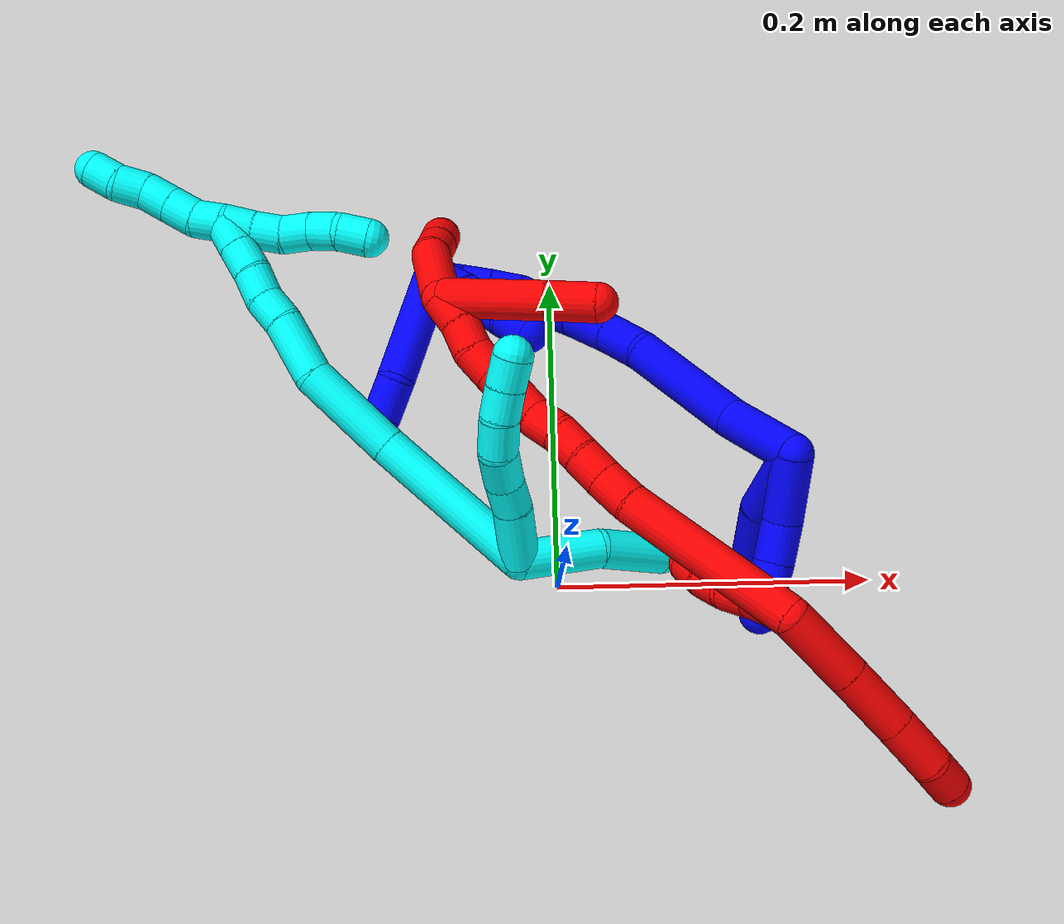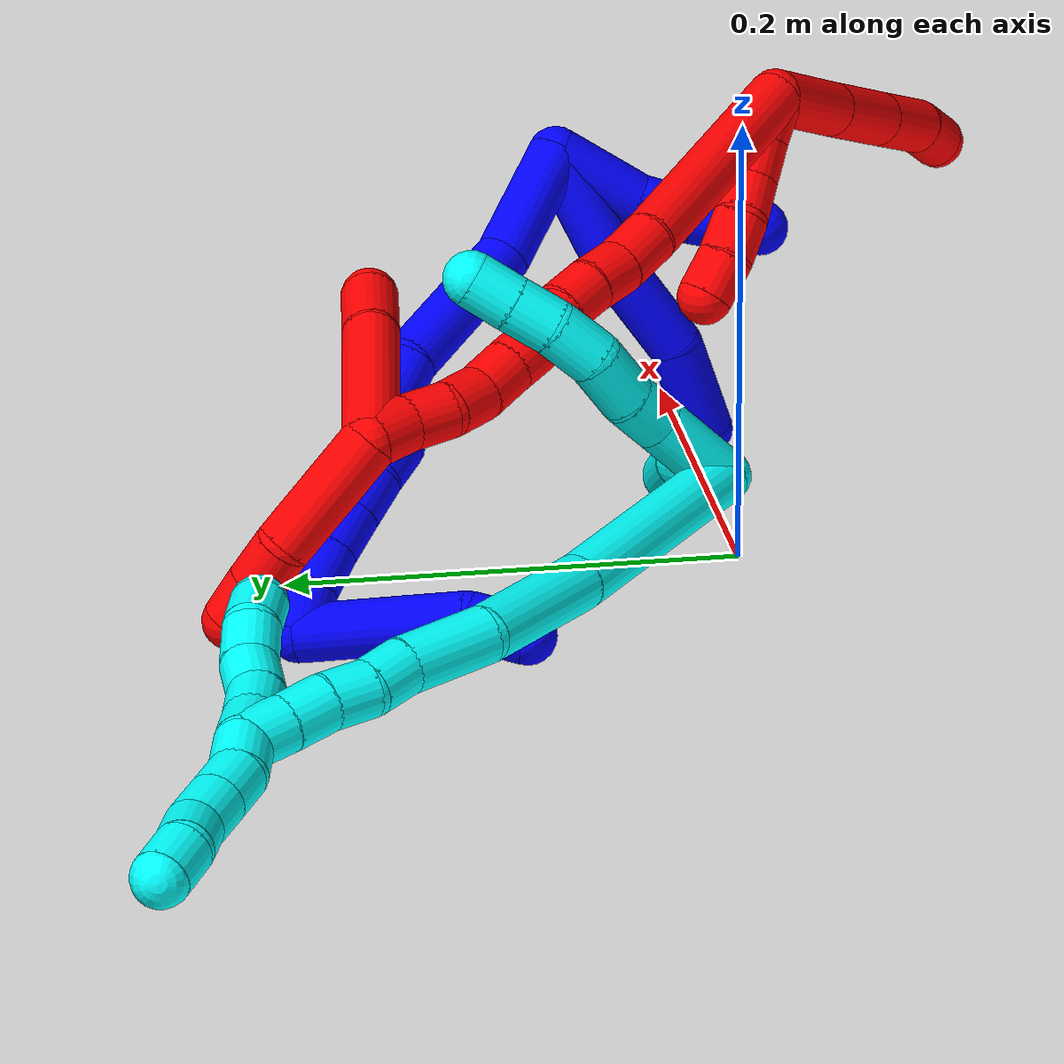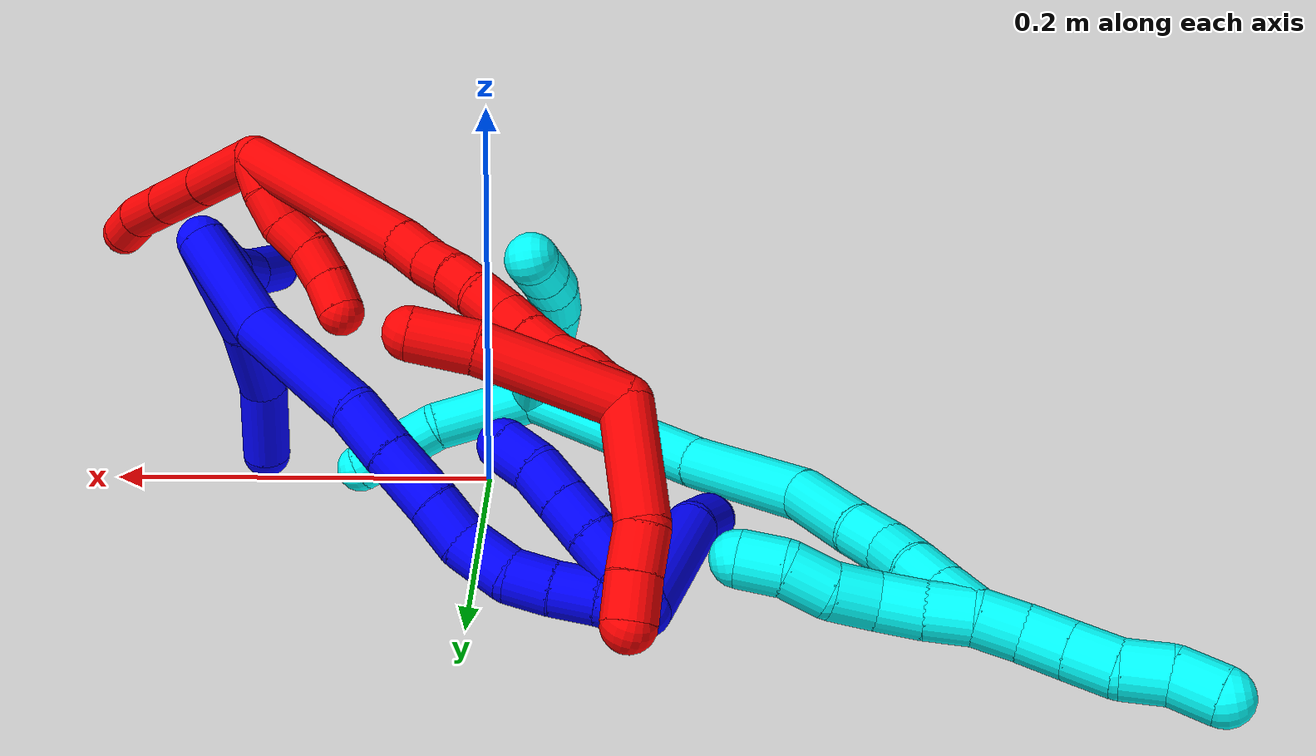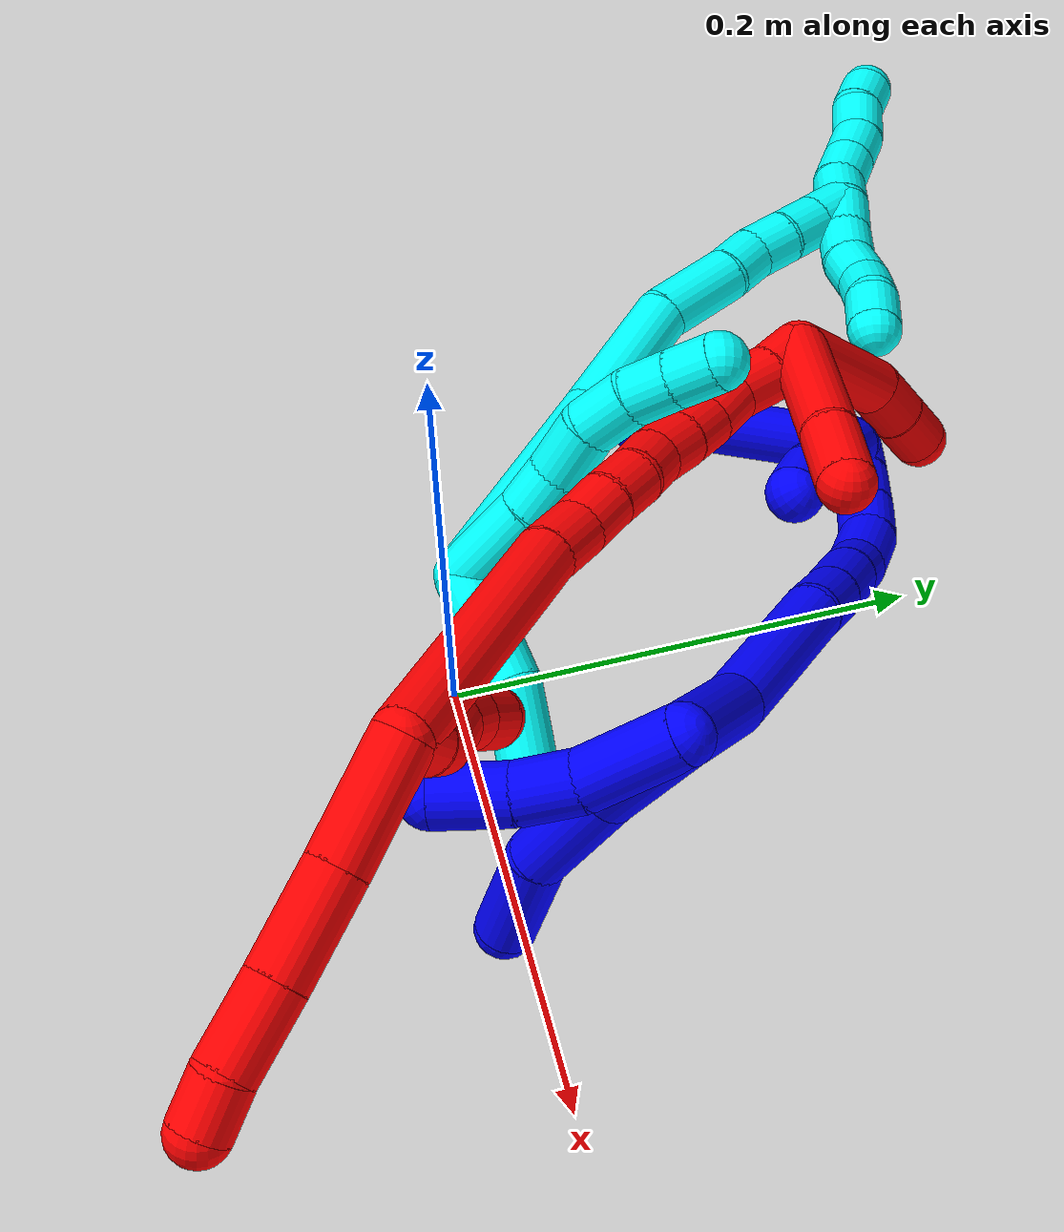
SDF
<sdf version="1.7">
 <world name="default">
  <plugin name="TubeGeneratorPlugin" filename="libtube_generator_plugin.so"/>
  <model name="photoneo_s_sensor">
   <static>1</static>
   <pose>0 0 2 1.57079 1.57079 3.14159</pose>
   <link name="link">
    <inertial><mass>0.1</mass></inertial>
    <sensor name="sensor" type="depth">
     <update_rate>30</update_rate>
     <camera>
      <horizontal_fov>1.22</horizontal_fov>
      <image><width>1920</width><height>1200</height><format>B8G8R8</format></image>
      <clip><near>0.1</near><far>4</far></clip>
      <depth_camera><output>points</output></depth_camera>
     </camera>
     <plugin name="camera_plugin" filename="libgazebo_ros_depth_camera.so">
      <baseline>0.2</baseline>
      <alwaysOn>1</alwaysOn>
      <updateRate>0.0</updateRate>
      <cameraName>camera_ir</cameraName>
      <imageTopicName>/camera/color/image_raw</imageTopicName>
      <cameraInfoTopicName>/camera/color/camera_info</cameraInfoTopicName>
      <depthImageTopicName>/camera/depth/image_raw</depthImageTopicName>
      <depthImageCameraInfoTopicName>/camera/depth/camera_info</depthImageCameraInfoTopicName>
      <pointCloudTopicName>/camera/depth/points</pointCloudTopicName>
      <frameName>fr_optical</frameName>
      <pointCloudCutoff>0.1</pointCloudCutoff>
      <pointCloudCutoffMax>2.0</pointCloudCutoffMax>
      <distortionK1>0</distortionK1>
      <distortionK2>0</distortionK2>
      <distortionK3>0</distortionK3>
      <distortionT1>0</distortionT1>
      <distortionT2>0</distortionT2>
      <CxPrime>0</CxPrime>
      <Cx>0</Cx>
      <Cy>0</Cy>
      <focalLength>0</focalLength>
      <hackBaseline>0</hackBaseline>
     </plugin>
    </sensor>
   </link>
  </model>
  <gravity>0 0 -9.8</gravity>
  <magnetic_field>6e-06 2.3e-05 -4.2e-05</magnetic_field>
  <atmosphere type="adiabatic"/>
  <physics name="default_physics" default="0" type="ode">
   <max_step_size>0.003</max_step_size>
   <real_time_factor>1</real_time_factor>
   <real_time_update_rate>1000</real_time_update_rate>
   <max_contacts>10000</max_contacts>
   <ode>
    <solver>
     <type>quick</type>
     <iters>100</iters>
     <sor>1.3</sor>
     <use_dynamic_moi_rescaling>0</use_dynamic_moi_rescaling>
    </solver>
    <constraints>
     <contact_max_correcting_vel>0</contact_max_correcting_vel>
     <contact_surface_layer>0.001</contact_surface_layer>
     <cfm>0</cfm>
     <erp>0.2</erp>
    </constraints>
   </ode>
  </physics>
  <scene><ambient>0.4 0.4 0.4 1</ambient><background>0.7 0.7 0.7 1</background><shadows>0</shadows></scene>
  <audio><device>default</device></audio>
  <spherical_coordinates>
   <surface_model>EARTH_WGS84</surface_model>
   <latitude_deg>0</latitude_deg>
   <longitude_deg>0</longitude_deg>
   <elevation>0</elevation>
   <heading_deg>0</heading_deg>
  </spherical_coordinates>
  <model name="bin">
   <static>1</static>
   <link name="bottom">
    <collision name="collision-bottom">
     <pose>0 0 -0.01 0 -0 0</pose>
     <geometry><box><size>0.8 0.6 0.02</size></box></geometry>
     <surface>
      <friction><ode><mu>100</mu><mu2>100</mu2></ode></friction>
      <contact><collide_bitmask>65535</collide_bitmask></contact>
     </surface>
    </collision>
   </link>
   <link name="west_wall">
    <collision name="collision-west_wall">
     <pose>-0.41 0 0.1 0 -0 0</pose>
     <geometry><box><size>0.02 0.6 0.2</size></box></geometry>
     <surface>
      <friction><ode><mu>100</mu><mu2>100</mu2></ode></friction>
      <contact><collide_bitmask>65535</collide_bitmask></contact>
     </surface>
    </collision>
   </link>
   <link name="east_wall">
    <collision name="collision-east_wall">
     <pose>0.41 0 0.1 0 -0 0</pose>
     <geometry><box><size>0.02 0.6 0.2</size></box></geometry>
     <surface>
      <friction><ode><mu>100</mu><mu2>100</mu2></ode></friction>
      <contact><collide_bitmask>65535</collide_bitmask></contact>
     </surface>
    </collision>
   </link>
   <link name="south_wall">
    <collision name="collision-south_wall">
     <pose>0 -0.31 0.1 0 -0 0</pose>
     <geometry><box><size>0.8 0.02 0.2</size></box></geometry>
     <surface>
      <friction><ode><mu>100</mu><mu2>100</mu2></ode></friction>
      <contact><collide_bitmask>65535</collide_bitmask></contact>
     </surface>
    </collision>
   </link>
   <link name="north_wall">
    <collision name="collision-north_wall">
     <pose>0 0.31 0.1 0 -0 0</pose>
     <geometry><box><size>0.8 0.02 0.2</size></box></geometry>
     <surface>
      <friction><ode><mu>100</mu><mu2>100</mu2></ode></friction>
      <contact><collide_bitmask>65535</collide_bitmask></contact>
     </surface>
    </collision>
   </link>
  </model>
  <model name="1">
   <static>0</static>
   <link name="1">
    <collision name="collision-cylinder-e_1_2_8">
     <pose>0.001882 0.003554 -0.028335 -3.01681 0.065812 -0.969933</pose>
     <geometry><cylinder><radius>0.0125</radius><length>0.057239</length></cylinder></geometry>
     <surface>
      <friction><ode><mu>1.16</mu><mu2>1.16</mu2><slip1>0</slip1><slip2>0</slip2></ode></friction>
      <contact><ode><kp>1e+06</kp><kd>1</kd><max_vel>0</max_vel><min_depth>0.001</min_depth></ode></contact>
     </surface>
    </collision>
    <visual name="visual-cylinder-e_1_2_8">
     <pose>0.001882 0.003554 -0.028335 -3.01681 0.065812 -0.969933</pose>
     <geometry><cylinder><radius>0.0125</radius><length>0.057239</length></cylinder></geometry>
     <material><ambient>0 0 1 1</ambient></material>
    </visual>
    <collision name="collision-cylinder-e_2_8_9">
     <pose>0.009485 0.005816 -0.079765 3.08572 0.242459 2.69062</pose>
     <geometry><cylinder><radius>0.0125</radius><length>0.047654</length></cylinder></geometry>
     <surface>
      <friction><ode><mu>1.16</mu><mu2>1.16</mu2><slip1>0</slip1><slip2>0</slip2></ode></friction>
      <contact><ode><kp>1e+06</kp><kd>1</kd><max_vel>0</max_vel><min_depth>0.001</min_depth></ode></contact>
     </surface>
    </collision>
    <visual name="visual-cylinder-e_2_8_9">
     <pose>0.009485 0.005816 -0.079765 3.08572 0.242459 2.69062</pose>
     <geometry><cylinder><radius>0.0125</radius><length>0.047654</length></cylinder></geometry>
     <material><ambient>0 0 1 1</ambient></material>
    </visual>
    <collision name="collision-cylinder-e_3_9_6">
     <pose>0.023561 0.009497 -0.123209 -2.90194 0.379489 -2.02164</pose>
     <geometry><cylinder><radius>0.0125</radius><length>0.045107</length></cylinder></geometry>
     <surface>
      <friction><ode><mu>1.16</mu><mu2>1.16</mu2><slip1>0</slip1><slip2>0</slip2></ode></friction>
      <contact><ode><kp>1e+06</kp><kd>1</kd><max_vel>0</max_vel><min_depth>0.001</min_depth></ode></contact>
     </surface>
    </collision>
    <visual name="visual-cylinder-e_3_9_6">
     <pose>0.023561 0.009497 -0.123209 -2.90194 0.379489 -2.02164</pose>
     <geometry><cylinder><radius>0.0125</radius><length>0.045107</length></cylinder></geometry>
     <material><ambient>0 0 1 1</ambient></material>
    </visual>
    <collision name="collision-cylinder-e_1_2_10">
     <pose>0.002536 -0.00901 -0.019284 2.70452 0.118575 0.522337</pose>
     <geometry><cylinder><radius>0.0125</radius><length>0.042871</length></cylinder></geometry>
     <surface>
      <friction><ode><mu>1.16</mu><mu2>1.16</mu2><slip1>0</slip1><slip2>0</slip2></ode></friction>
      <contact><ode><kp>1e+06</kp><kd>1</kd><max_vel>0</max_vel><min_depth>0.001</min_depth></ode></contact>
     </surface>
    </collision>
    <visual name="visual-cylinder-e_1_2_10">
     <pose>0.002536 -0.00901 -0.019284 2.70452 0.118575 0.522337</pose>
     <geometry><cylinder><radius>0.0125</radius><length>0.042871</length></cylinder></geometry>
     <material><ambient>0 0 1 1</ambient></material>
    </visual>
    <collision name="collision-cylinder-e_2_10_11">
     <pose>0.004616 -0.026137 -0.048638 2.46319 -0.035195 -0.099675</pose>
     <geometry><cylinder><radius>0.0125</radius><length>0.025886</length></cylinder></geometry>
     <surface>
      <friction><ode><mu>1.16</mu><mu2>1.16</mu2><slip1>0</slip1><slip2>0</slip2></ode></friction>
      <contact><ode><kp>1e+06</kp><kd>1</kd><max_vel>0</max_vel><min_depth>0.001</min_depth></ode></contact>
     </surface>
    </collision>
    <visual name="visual-cylinder-e_2_10_11">
     <pose>0.004616 -0.026137 -0.048638 2.46319 -0.035195 -0.099675</pose>
     <geometry><cylinder><radius>0.0125</radius><length>0.025886</length></cylinder></geometry>
     <material><ambient>0 0 1 1</ambient></material>
    </visual>
    <collision name="collision-cylinder-e_3_11_5">
     <pose>0.001572 -0.045377 -0.069368 2.33486 -0.166474 -0.386117</pose>
     <geometry><cylinder><radius>0.0125</radius><length>0.031244</length></cylinder></geometry>
     <surface>
      <friction><ode><mu>1.16</mu><mu2>1.16</mu2><slip1>0</slip1><slip2>0</slip2></ode></friction>
      <contact><ode><kp>1e+06</kp><kd>1</kd><max_vel>0</max_vel><min_depth>0.001</min_depth></ode></contact>
     </surface>
    </collision>
    <visual name="visual-cylinder-e_3_11_5">
     <pose>0.001572 -0.045377 -0.069368 2.33486 -0.166474 -0.386117</pose>
     <geometry><cylinder><radius>0.0125</radius><length>0.031244</length></cylinder></geometry>
     <material><ambient>0 0 1 1</ambient></material>
    </visual>
    <collision name="collision-cylinder-e_1_2_12">
     <pose>-0.010447 0.023293 -0.011432 -2.02704 -0.382771 0.6029</pose>
     <geometry><cylinder><radius>0.0125</radius><length>0.055943</length></cylinder></geometry>
     <surface>
      <friction><ode><mu>1.16</mu><mu2>1.16</mu2><slip1>0</slip1><slip2>0</slip2></ode></friction>
      <contact><ode><kp>1e+06</kp><kd>1</kd><max_vel>0</max_vel><min_depth>0.001</min_depth></ode></contact>
     </surface>
    </collision>
    <visual name="visual-cylinder-e_1_2_12">
     <pose>-0.010447 0.023293 -0.011432 -2.02704 -0.382771 0.6029</pose>
     <geometry><cylinder><radius>0.0125</radius><length>0.055943</length></cylinder></geometry>
     <material><ambient>0 0 1 1</ambient></material>
    </visual>
    <collision name="collision-cylinder-e_2_12_13">
     <pose>-0.042959 0.076684 -0.0282 -1.74626 -0.625224 0.735979</pose>
     <geometry><cylinder><radius>0.0125</radius><length>0.075398</length></cylinder></geometry>
     <surface>
      <friction><ode><mu>1.16</mu><mu2>1.16</mu2><slip1>0</slip1><slip2>0</slip2></ode></friction>
      <contact><ode><kp>1e+06</kp><kd>1</kd><max_vel>0</max_vel><min_depth>0.001</min_depth></ode></contact>
     </surface>
    </collision>
    <visual name="visual-cylinder-e_2_12_13">
     <pose>-0.042959 0.076684 -0.0282 -1.74626 -0.625224 0.735979</pose>
     <geometry><cylinder><radius>0.0125</radius><length>0.075398</length></cylinder></geometry>
     <material><ambient>0 0 1 1</ambient></material>
    </visual>
    <collision name="collision-cylinder-e_3_13_14">
     <pose>-0.071386 0.118078 -0.038792 -2.00635 -0.472196 0.721601</pose>
     <geometry><cylinder><radius>0.0125</radius><length>0.02798</length></cylinder></geometry>
     <surface>
      <friction><ode><mu>1.16</mu><mu2>1.16</mu2><slip1>0</slip1><slip2>0</slip2></ode></friction>
      <contact><ode><kp>1e+06</kp><kd>1</kd><max_vel>0</max_vel><min_depth>0.001</min_depth></ode></contact>
     </surface>
    </collision>
    <visual name="visual-cylinder-e_3_13_14">
     <pose>-0.071386 0.118078 -0.038792 -2.00635 -0.472196 0.721601</pose>
     <geometry><cylinder><radius>0.0125</radius><length>0.02798</length></cylinder></geometry>
     <material><ambient>0 0 1 1</ambient></material>
    </visual>
    <collision name="collision-cylinder-e_4_14_15">
     <pose>-0.085334 0.141706 -0.050606 -2.05947 -0.497488 0.799888</pose>
     <geometry><cylinder><radius>0.0125</radius><length>0.031787</length></cylinder></geometry>
     <surface>
      <friction><ode><mu>1.16</mu><mu2>1.16</mu2><slip1>0</slip1><slip2>0</slip2></ode></friction>
      <contact><ode><kp>1e+06</kp><kd>1</kd><max_vel>0</max_vel><min_depth>0.001</min_depth></ode></contact>
     </surface>
    </collision>
    <visual name="visual-cylinder-e_4_14_15">
     <pose>-0.085334 0.141706 -0.050606 -2.05947 -0.497488 0.799888</pose>
     <geometry><cylinder><radius>0.0125</radius><length>0.031787</length></cylinder></geometry>
     <material><ambient>0 0 1 1</ambient></material>
    </visual>
    <collision name="collision-cylinder-e_5_15_16">
     <pose>-0.097628 0.162544 -0.062297 -2.11385 -0.442676 0.7587</pose>
     <geometry><cylinder><radius>0.0125</radius><length>0.02199</length></cylinder></geometry>
     <surface>
      <friction><ode><mu>1.16</mu><mu2>1.16</mu2><slip1>0</slip1><slip2>0</slip2></ode></friction>
      <contact><ode><kp>1e+06</kp><kd>1</kd><max_vel>0</max_vel><min_depth>0.001</min_depth></ode></contact>
     </surface>
    </collision>
    <visual name="visual-cylinder-e_5_15_16">
     <pose>-0.097628 0.162544 -0.062297 -2.11385 -0.442676 0.7587</pose>
     <geometry><cylinder><radius>0.0125</radius><length>0.02199</length></cylinder></geometry>
     <material><ambient>0 0 1 1</ambient></material>
    </visual>
    <collision name="collision-cylinder-e_6_16_17">
     <pose>-0.111158 0.180295 -0.071188 -1.95685 -0.7238 1.02481</pose>
     <geometry><cylinder><radius>0.0125</radius><length>0.026636</length></cylinder></geometry>
     <surface>
      <friction><ode><mu>1.16</mu><mu2>1.16</mu2><slip1>0</slip1><slip2>0</slip2></ode></friction>
      <contact><ode><kp>1e+06</kp><kd>1</kd><max_vel>0</max_vel><min_depth>0.001</min_depth></ode></contact>
     </surface>
    </collision>
    <visual name="visual-cylinder-e_6_16_17">
     <pose>-0.111158 0.180295 -0.071188 -1.95685 -0.7238 1.02481</pose>
     <geometry><cylinder><radius>0.0125</radius><length>0.026636</length></cylinder></geometry>
     <material><ambient>0 0 1 1</ambient></material>
    </visual>
    <collision name="collision-cylinder-e_7_17_18">
     <pose>-0.128654 0.193685 -0.077929 -2.19457 -1.03877 1.68018</pose>
     <geometry><cylinder><radius>0.0125</radius><length>0.020136</length></cylinder></geometry>
     <surface>
      <friction><ode><mu>1.16</mu><mu2>1.16</mu2><slip1>0</slip1><slip2>0</slip2></ode></friction>
      <contact><ode><kp>1e+06</kp><kd>1</kd><max_vel>0</max_vel><min_depth>0.001</min_depth></ode></contact>
     </surface>
    </collision>
    <visual name="visual-cylinder-e_7_17_18">
     <pose>-0.128654 0.193685 -0.077929 -2.19457 -1.03877 1.68018</pose>
     <geometry><cylinder><radius>0.0125</radius><length>0.020136</length></cylinder></geometry>
     <material><ambient>0 0 1 1</ambient></material>
    </visual>
    <collision name="collision-cylinder-e_8_18_19">
     <pose>-0.14637 0.201196 -0.083665 -2.25642 -1.12242 1.84957</pose>
     <geometry><cylinder><radius>0.0125</radius><length>0.020062</length></cylinder></geometry>
     <surface>
      <friction><ode><mu>1.16</mu><mu2>1.16</mu2><slip1>0</slip1><slip2>0</slip2></ode></friction>
      <contact><ode><kp>1e+06</kp><kd>1</kd><max_vel>0</max_vel><min_depth>0.001</min_depth></ode></contact>
     </surface>
    </collision>
    <visual name="visual-cylinder-e_8_18_19">
     <pose>-0.14637 0.201196 -0.083665 -2.25642 -1.12242 1.84957</pose>
     <geometry><cylinder><radius>0.0125</radius><length>0.020062</length></cylinder></geometry>
     <material><ambient>0 0 1 1</ambient></material>
    </visual>
    <collision name="collision-cylinder-e_9_19_1">
     <pose>-0.164157 0.20815 -0.089779 -2.32341 -1.05882 1.86622</pose>
     <geometry><cylinder><radius>0.0125</radius><length>0.020069</length></cylinder></geometry>
     <surface>
      <friction><ode><mu>1.16</mu><mu2>1.16</mu2><slip1>0</slip1><slip2>0</slip2></ode></friction>
      <contact><ode><kp>1e+06</kp><kd>1</kd><max_vel>0</max_vel><min_depth>0.001</min_depth></ode></contact>
     </surface>
    </collision>
    <visual name="visual-cylinder-e_9_19_1">
     <pose>-0.164157 0.20815 -0.089779 -2.32341 -1.05882 1.86622</pose>
     <geometry><cylinder><radius>0.0125</radius><length>0.020069</length></cylinder></geometry>
     <material><ambient>0 0 1 1</ambient></material>
    </visual>
    <collision name="collision-cylinder-e_1_1_20">
     <pose>-0.170291 0.204403 -0.086865 0.863218 0.264461 0.122365</pose>
     <geometry><cylinder><radius>0.0125</radius><length>0.02</length></cylinder></geometry>
     <surface>
      <friction><ode><mu>1.16</mu><mu2>1.16</mu2><slip1>0</slip1><slip2>0</slip2></ode></friction>
      <contact><ode><kp>1e+06</kp><kd>1</kd><max_vel>0</max_vel><min_depth>0.001</min_depth></ode></contact>
     </surface>
    </collision>
    <visual name="visual-cylinder-e_1_1_20">
     <pose>-0.170291 0.204403 -0.086865 0.863218 0.264461 0.122365</pose>
     <geometry><cylinder><radius>0.0125</radius><length>0.02</length></cylinder></geometry>
     <material><ambient>0 0 1 1</ambient></material>
    </visual>
    <collision name="collision-cylinder-e_2_20_21">
     <pose>-0.16324 0.189011 -0.076668 1.11764 0.459705 0.290567</pose>
     <geometry><cylinder><radius>0.0125</radius><length>0.02</length></cylinder></geometry>
     <surface>
      <friction><ode><mu>1.16</mu><mu2>1.16</mu2><slip1>0</slip1><slip2>0</slip2></ode></friction>
      <contact><ode><kp>1e+06</kp><kd>1</kd><max_vel>0</max_vel><min_depth>0.001</min_depth></ode></contact>
     </surface>
    </collision>
    <visual name="visual-cylinder-e_2_20_21">
     <pose>-0.16324 0.189011 -0.076668 1.11764 0.459705 0.290567</pose>
     <geometry><cylinder><radius>0.0125</radius><length>0.02</length></cylinder></geometry>
     <material><ambient>0 0 1 1</ambient></material>
    </visual>
    <collision name="collision-cylinder-e_3_21_22">
     <pose>-0.154304 0.172658 -0.069436 1.1913 0.466665 0.319416</pose>
     <geometry><cylinder><radius>0.0125</radius><length>0.02</length></cylinder></geometry>
     <surface>
      <friction><ode><mu>1.16</mu><mu2>1.16</mu2><slip1>0</slip1><slip2>0</slip2></ode></friction>
      <contact><ode><kp>1e+06</kp><kd>1</kd><max_vel>0</max_vel><min_depth>0.001</min_depth></ode></contact>
     </surface>
    </collision>
    <visual name="visual-cylinder-e_3_21_22">
     <pose>-0.154304 0.172658 -0.069436 1.1913 0.466665 0.319416</pose>
     <geometry><cylinder><radius>0.0125</radius><length>0.02</length></cylinder></geometry>
     <material><ambient>0 0 1 1</ambient></material>
    </visual>
    <collision name="collision-cylinder-e_4_22_23">
     <pose>-0.145328 0.156012 -0.062929 1.20508 0.464161 0.322321</pose>
     <geometry><cylinder><radius>0.0125</radius><length>0.02</length></cylinder></geometry>
     <surface>
      <friction><ode><mu>1.16</mu><mu2>1.16</mu2><slip1>0</slip1><slip2>0</slip2></ode></friction>
      <contact><ode><kp>1e+06</kp><kd>1</kd><max_vel>0</max_vel><min_depth>0.001</min_depth></ode></contact>
     </surface>
    </collision>
    <visual name="visual-cylinder-e_4_22_23">
     <pose>-0.145328 0.156012 -0.062929 1.20508 0.464161 0.322321</pose>
     <geometry><cylinder><radius>0.0125</radius><length>0.02</length></cylinder></geometry>
     <material><ambient>0 0 1 1</ambient></material>
    </visual>
    <collision name="collision-cylinder-e_5_23_4">
     <pose>-0.134437 0.140266 -0.057691 1.30161 0.696417 0.539361</pose>
     <geometry><cylinder><radius>0.0125</radius><length>0.02</length></cylinder></geometry>
     <surface>
      <friction><ode><mu>1.16</mu><mu2>1.16</mu2><slip1>0</slip1><slip2>0</slip2></ode></friction>
      <contact><ode><kp>1e+06</kp><kd>1</kd><max_vel>0</max_vel><min_depth>0.001</min_depth></ode></contact>
     </surface>
    </collision>
    <visual name="visual-cylinder-e_5_23_4">
     <pose>-0.134437 0.140266 -0.057691 1.30161 0.696417 0.539361</pose>
     <geometry><cylinder><radius>0.0125</radius><length>0.02</length></cylinder></geometry>
     <material><ambient>0 0 1 1</ambient></material>
    </visual>
    <collision name="collision-cylinder-e_1_1_24">
     <pose>-0.183269 0.180701 -0.110428 2.07902 -0.283854 -0.477047</pose>
     <geometry><cylinder><radius>0.0125</radius><length>0.074017</length></cylinder></geometry>
     <surface>
      <friction><ode><mu>1.16</mu><mu2>1.16</mu2><slip1>0</slip1><slip2>0</slip2></ode></friction>
      <contact><ode><kp>1e+06</kp><kd>1</kd><max_vel>0</max_vel><min_depth>0.001</min_depth></ode></contact>
     </surface>
    </collision>
    <visual name="visual-cylinder-e_1_1_24">
     <pose>-0.183269 0.180701 -0.110428 2.07902 -0.283854 -0.477047</pose>
     <geometry><cylinder><radius>0.0125</radius><length>0.074017</length></cylinder></geometry>
     <material><ambient>0 0 1 1</ambient></material>
    </visual>
    <collision name="collision-cylinder-e_2_24_3">
     <pose>-0.196634 0.141361 -0.137247 2.42493 -0.23301 -0.605792</pose>
     <geometry><cylinder><radius>0.0125</radius><length>0.025983</length></cylinder></geometry>
     <surface>
      <friction><ode><mu>1.16</mu><mu2>1.16</mu2><slip1>0</slip1><slip2>0</slip2></ode></friction>
      <contact><ode><kp>1e+06</kp><kd>1</kd><max_vel>0</max_vel><min_depth>0.001</min_depth></ode></contact>
     </surface>
    </collision>
    <visual name="visual-cylinder-e_2_24_3">
     <pose>-0.196634 0.141361 -0.137247 2.42493 -0.23301 -0.605792</pose>
     <geometry><cylinder><radius>0.0125</radius><length>0.025983</length></cylinder></geometry>
     <material><ambient>0 0 1 1</ambient></material>
    </visual>
    <collision name="collision-sphere-3">
     <pose>-0.199634 0.133058 -0.146778 0 -0 0</pose>
     <geometry><sphere><radius>0.0125</radius></sphere></geometry>
     <surface>
      <friction><ode><mu>1.16</mu><mu2>1.16</mu2><slip1>0</slip1><slip2>0</slip2></ode></friction>
      <contact><ode><kp>1e+06</kp><kd>1</kd><max_vel>0</max_vel><min_depth>0.001</min_depth></ode></contact>
     </surface>
    </collision>
    <visual name="visual-sphere-3">
     <pose>-0.199634 0.133058 -0.146778 0 -0 0</pose>
     <geometry><sphere><radius>0.0125</radius></sphere></geometry>
     <material><ambient>0 0 1 1</ambient></material>
    </visual>
    <collision name="collision-sphere-24">
     <pose>-0.193634 0.149664 -0.127716 0 -0 0</pose>
     <geometry><sphere><radius>0.0125</radius></sphere></geometry>
     <surface>
      <friction><ode><mu>1.16</mu><mu2>1.16</mu2><slip1>0</slip1><slip2>0</slip2></ode></friction>
      <contact><ode><kp>1e+06</kp><kd>1</kd><max_vel>0</max_vel><min_depth>0.001</min_depth></ode></contact>
     </surface>
    </collision>
    <visual name="visual-sphere-24">
     <pose>-0.193634 0.149664 -0.127716 0 -0 0</pose>
     <geometry><sphere><radius>0.0125</radius></sphere></geometry>
     <material><ambient>0 0 1 1</ambient></material>
    </visual>
    <collision name="collision-sphere-4">
     <pose>-0.128022 0.132871 -0.055651 0 -0 0</pose>
     <geometry><sphere><radius>0.0125</radius></sphere></geometry>
     <surface>
      <friction><ode><mu>1.16</mu><mu2>1.16</mu2><slip1>0</slip1><slip2>0</slip2></ode></friction>
      <contact><ode><kp>1e+06</kp><kd>1</kd><max_vel>0</max_vel><min_depth>0.001</min_depth></ode></contact>
     </surface>
    </collision>
    <visual name="visual-sphere-4">
     <pose>-0.128022 0.132871 -0.055651 0 -0 0</pose>
     <geometry><sphere><radius>0.0125</radius></sphere></geometry>
     <material><ambient>0 0 1 1</ambient></material>
    </visual>
    <collision name="collision-sphere-23">
     <pose>-0.140852 0.147661 -0.059732 0 -0 0</pose>
     <geometry><sphere><radius>0.0125</radius></sphere></geometry>
     <surface>
      <friction><ode><mu>1.16</mu><mu2>1.16</mu2><slip1>0</slip1><slip2>0</slip2></ode></friction>
      <contact><ode><kp>1e+06</kp><kd>1</kd><max_vel>0</max_vel><min_depth>0.001</min_depth></ode></contact>
     </surface>
    </collision>
    <visual name="visual-sphere-23">
     <pose>-0.140852 0.147661 -0.059732 0 -0 0</pose>
     <geometry><sphere><radius>0.0125</radius></sphere></geometry>
     <material><ambient>0 0 1 1</ambient></material>
    </visual>
    <collision name="collision-sphere-22">
     <pose>-0.149805 0.164363 -0.066127 0 -0 0</pose>
     <geometry><sphere><radius>0.0125</radius></sphere></geometry>
     <surface>
      <friction><ode><mu>1.16</mu><mu2>1.16</mu2><slip1>0</slip1><slip2>0</slip2></ode></friction>
      <contact><ode><kp>1e+06</kp><kd>1</kd><max_vel>0</max_vel><min_depth>0.001</min_depth></ode></contact>
     </surface>
    </collision>
    <visual name="visual-sphere-22">
     <pose>-0.149805 0.164363 -0.066127 0 -0 0</pose>
     <geometry><sphere><radius>0.0125</radius></sphere></geometry>
     <material><ambient>0 0 1 1</ambient></material>
    </visual>
    <collision name="collision-sphere-21">
     <pose>-0.158803 0.180953 -0.072744 0 -0 0</pose>
     <geometry><sphere><radius>0.0125</radius></sphere></geometry>
     <surface>
      <friction><ode><mu>1.16</mu><mu2>1.16</mu2><slip1>0</slip1><slip2>0</slip2></ode></friction>
      <contact><ode><kp>1e+06</kp><kd>1</kd><max_vel>0</max_vel><min_depth>0.001</min_depth></ode></contact>
     </surface>
    </collision>
    <visual name="visual-sphere-21">
     <pose>-0.158803 0.180953 -0.072744 0 -0 0</pose>
     <geometry><sphere><radius>0.0125</radius></sphere></geometry>
     <material><ambient>0 0 1 1</ambient></material>
    </visual>
    <collision name="collision-sphere-20">
     <pose>-0.167677 0.197068 -0.080591 0 -0 0</pose>
     <geometry><sphere><radius>0.0125</radius></sphere></geometry>
     <surface>
      <friction><ode><mu>1.16</mu><mu2>1.16</mu2><slip1>0</slip1><slip2>0</slip2></ode></friction>
      <contact><ode><kp>1e+06</kp><kd>1</kd><max_vel>0</max_vel><min_depth>0.001</min_depth></ode></contact>
     </surface>
    </collision>
    <visual name="visual-sphere-20">
     <pose>-0.167677 0.197068 -0.080591 0 -0 0</pose>
     <geometry><sphere><radius>0.0125</radius></sphere></geometry>
     <material><ambient>0 0 1 1</ambient></material>
    </visual>
    <collision name="collision-sphere-11">
     <pose>0.004161 -0.034254 -0.058709 0 -0 0</pose>
     <geometry><sphere><radius>0.0125</radius></sphere></geometry>
     <surface>
      <friction><ode><mu>1.16</mu><mu2>1.16</mu2><slip1>0</slip1><slip2>0</slip2></ode></friction>
      <contact><ode><kp>1e+06</kp><kd>1</kd><max_vel>0</max_vel><min_depth>0.001</min_depth></ode></contact>
     </surface>
    </collision>
    <visual name="visual-sphere-11">
     <pose>0.004161 -0.034254 -0.058709 0 -0 0</pose>
     <geometry><sphere><radius>0.0125</radius></sphere></geometry>
     <material><ambient>0 0 1 1</ambient></material>
    </visual>
    <collision name="collision-sphere-10">
     <pose>0.005071 -0.018019 -0.038568 0 -0 0</pose>
     <geometry><sphere><radius>0.0125</radius></sphere></geometry>
     <surface>
      <friction><ode><mu>1.16</mu><mu2>1.16</mu2><slip1>0</slip1><slip2>0</slip2></ode></friction>
      <contact><ode><kp>1e+06</kp><kd>1</kd><max_vel>0</max_vel><min_depth>0.001</min_depth></ode></contact>
     </surface>
    </collision>
    <visual name="visual-sphere-10">
     <pose>0.005071 -0.018019 -0.038568 0 -0 0</pose>
     <geometry><sphere><radius>0.0125</radius></sphere></geometry>
     <material><ambient>0 0 1 1</ambient></material>
    </visual>
    <collision name="collision-sphere-6">
     <pose>0.031915 0.01447 -0.143559 0 -0 0</pose>
     <geometry><sphere><radius>0.0125</radius></sphere></geometry>
     <surface>
      <friction><ode><mu>1.16</mu><mu2>1.16</mu2><slip1>0</slip1><slip2>0</slip2></ode></friction>
      <contact><ode><kp>1e+06</kp><kd>1</kd><max_vel>0</max_vel><min_depth>0.001</min_depth></ode></contact>
     </surface>
    </collision>
    <visual name="visual-sphere-6">
     <pose>0.031915 0.01447 -0.143559 0 -0 0</pose>
     <geometry><sphere><radius>0.0125</radius></sphere></geometry>
     <material><ambient>0 0 1 1</ambient></material>
    </visual>
    <collision name="collision-sphere-9">
     <pose>0.015206 0.004525 -0.102859 0 -0 0</pose>
     <geometry><sphere><radius>0.0125</radius></sphere></geometry>
     <surface>
      <friction><ode><mu>1.16</mu><mu2>1.16</mu2><slip1>0</slip1><slip2>0</slip2></ode></friction>
      <contact><ode><kp>1e+06</kp><kd>1</kd><max_vel>0</max_vel><min_depth>0.001</min_depth></ode></contact>
     </surface>
    </collision>
    <visual name="visual-sphere-9">
     <pose>0.015206 0.004525 -0.102859 0 -0 0</pose>
     <geometry><sphere><radius>0.0125</radius></sphere></geometry>
     <material><ambient>0 0 1 1</ambient></material>
    </visual>
    <collision name="collision-sphere-2">
     <geometry><sphere><radius>0.0125</radius></sphere></geometry>
     <surface>
      <friction><ode><mu>1.16</mu><mu2>1.16</mu2><slip1>0</slip1><slip2>0</slip2></ode></friction>
      <contact><ode><kp>1e+06</kp><kd>1</kd><max_vel>0</max_vel><min_depth>0.001</min_depth></ode></contact>
     </surface>
    </collision>
    <visual name="visual-sphere-2">
     <geometry><sphere><radius>0.0125</radius></sphere></geometry>
     <material><ambient>0 0 1 1</ambient></material>
    </visual>
    <collision name="collision-sphere-19">
     <pose>-0.155409 0.204562 -0.086419 0 -0 0</pose>
     <geometry><sphere><radius>0.0125</radius></sphere></geometry>
     <surface>
      <friction><ode><mu>1.16</mu><mu2>1.16</mu2><slip1>0</slip1><slip2>0</slip2></ode></friction>
      <contact><ode><kp>1e+06</kp><kd>1</kd><max_vel>0</max_vel><min_depth>0.001</min_depth></ode></contact>
     </surface>
    </collision>
    <visual name="visual-sphere-19">
     <pose>-0.155409 0.204562 -0.086419 0 -0 0</pose>
     <geometry><sphere><radius>0.0125</radius></sphere></geometry>
     <material><ambient>0 0 1 1</ambient></material>
    </visual>
    <collision name="collision-sphere-8">
     <pose>0.003764 0.007108 -0.056671 0 -0 0</pose>
     <geometry><sphere><radius>0.0125</radius></sphere></geometry>
     <surface>
      <friction><ode><mu>1.16</mu><mu2>1.16</mu2><slip1>0</slip1><slip2>0</slip2></ode></friction>
      <contact><ode><kp>1e+06</kp><kd>1</kd><max_vel>0</max_vel><min_depth>0.001</min_depth></ode></contact>
     </surface>
    </collision>
    <visual name="visual-sphere-8">
     <pose>0.003764 0.007108 -0.056671 0 -0 0</pose>
     <geometry><sphere><radius>0.0125</radius></sphere></geometry>
     <material><ambient>0 0 1 1</ambient></material>
    </visual>
    <collision name="collision-sphere-5">
     <pose>-0.001017 -0.056501 -0.080027 0 -0 0</pose>
     <geometry><sphere><radius>0.0125</radius></sphere></geometry>
     <surface>
      <friction><ode><mu>1.16</mu><mu2>1.16</mu2><slip1>0</slip1><slip2>0</slip2></ode></friction>
      <contact><ode><kp>1e+06</kp><kd>1</kd><max_vel>0</max_vel><min_depth>0.001</min_depth></ode></contact>
     </surface>
    </collision>
    <visual name="visual-sphere-5">
     <pose>-0.001017 -0.056501 -0.080027 0 -0 0</pose>
     <geometry><sphere><radius>0.0125</radius></sphere></geometry>
     <material><ambient>0 0 1 1</ambient></material>
    </visual>
    <collision name="collision-sphere-12">
     <pose>-0.020894 0.046586 -0.022864 0 -0 0</pose>
     <geometry><sphere><radius>0.0125</radius></sphere></geometry>
     <surface>
      <friction><ode><mu>1.16</mu><mu2>1.16</mu2><slip1>0</slip1><slip2>0</slip2></ode></friction>
      <contact><ode><kp>1e+06</kp><kd>1</kd><max_vel>0</max_vel><min_depth>0.001</min_depth></ode></contact>
     </surface>
    </collision>
    <visual name="visual-sphere-12">
     <pose>-0.020894 0.046586 -0.022864 0 -0 0</pose>
     <geometry><sphere><radius>0.0125</radius></sphere></geometry>
     <material><ambient>0 0 1 1</ambient></material>
    </visual>
    <collision name="collision-sphere-13">
     <pose>-0.065023 0.106782 -0.033536 0 -0 0</pose>
     <geometry><sphere><radius>0.0125</radius></sphere></geometry>
     <surface>
      <friction><ode><mu>1.16</mu><mu2>1.16</mu2><slip1>0</slip1><slip2>0</slip2></ode></friction>
      <contact><ode><kp>1e+06</kp><kd>1</kd><max_vel>0</max_vel><min_depth>0.001</min_depth></ode></contact>
     </surface>
    </collision>
    <visual name="visual-sphere-13">
     <pose>-0.065023 0.106782 -0.033536 0 -0 0</pose>
     <geometry><sphere><radius>0.0125</radius></sphere></geometry>
     <material><ambient>0 0 1 1</ambient></material>
    </visual>
    <collision name="collision-sphere-14">
     <pose>-0.077749 0.129374 -0.044049 0 -0 0</pose>
     <geometry><sphere><radius>0.0125</radius></sphere></geometry>
     <surface>
      <friction><ode><mu>1.16</mu><mu2>1.16</mu2><slip1>0</slip1><slip2>0</slip2></ode></friction>
      <contact><ode><kp>1e+06</kp><kd>1</kd><max_vel>0</max_vel><min_depth>0.001</min_depth></ode></contact>
     </surface>
    </collision>
    <visual name="visual-sphere-14">
     <pose>-0.077749 0.129374 -0.044049 0 -0 0</pose>
     <geometry><sphere><radius>0.0125</radius></sphere></geometry>
     <material><ambient>0 0 1 1</ambient></material>
    </visual>
    <collision name="collision-sphere-15">
     <pose>-0.092919 0.154038 -0.057163 0 -0 0</pose>
     <geometry><sphere><radius>0.0125</radius></sphere></geometry>
     <surface>
      <friction><ode><mu>1.16</mu><mu2>1.16</mu2><slip1>0</slip1><slip2>0</slip2></ode></friction>
      <contact><ode><kp>1e+06</kp><kd>1</kd><max_vel>0</max_vel><min_depth>0.001</min_depth></ode></contact>
     </surface>
    </collision>
    <visual name="visual-sphere-15">
     <pose>-0.092919 0.154038 -0.057163 0 -0 0</pose>
     <geometry><sphere><radius>0.0125</radius></sphere></geometry>
     <material><ambient>0 0 1 1</ambient></material>
    </visual>
    <collision name="collision-sphere-16">
     <pose>-0.102338 0.17105 -0.067431 0 -0 0</pose>
     <geometry><sphere><radius>0.0125</radius></sphere></geometry>
     <surface>
      <friction><ode><mu>1.16</mu><mu2>1.16</mu2><slip1>0</slip1><slip2>0</slip2></ode></friction>
      <contact><ode><kp>1e+06</kp><kd>1</kd><max_vel>0</max_vel><min_depth>0.001</min_depth></ode></contact>
     </surface>
    </collision>
    <visual name="visual-sphere-16">
     <pose>-0.102338 0.17105 -0.067431 0 -0 0</pose>
     <geometry><sphere><radius>0.0125</radius></sphere></geometry>
     <material><ambient>0 0 1 1</ambient></material>
    </visual>
    <collision name="collision-sphere-17">
     <pose>-0.119978 0.18954 -0.074946 0 -0 0</pose>
     <geometry><sphere><radius>0.0125</radius></sphere></geometry>
     <surface>
      <friction><ode><mu>1.16</mu><mu2>1.16</mu2><slip1>0</slip1><slip2>0</slip2></ode></friction>
      <contact><ode><kp>1e+06</kp><kd>1</kd><max_vel>0</max_vel><min_depth>0.001</min_depth></ode></contact>
     </surface>
    </collision>
    <visual name="visual-sphere-17">
     <pose>-0.119978 0.18954 -0.074946 0 -0 0</pose>
     <geometry><sphere><radius>0.0125</radius></sphere></geometry>
     <material><ambient>0 0 1 1</ambient></material>
    </visual>
    <collision name="collision-sphere-18">
     <pose>-0.13733 0.19783 -0.080912 0 -0 0</pose>
     <geometry><sphere><radius>0.0125</radius></sphere></geometry>
     <surface>
      <friction><ode><mu>1.16</mu><mu2>1.16</mu2><slip1>0</slip1><slip2>0</slip2></ode></friction>
      <contact><ode><kp>1e+06</kp><kd>1</kd><max_vel>0</max_vel><min_depth>0.001</min_depth></ode></contact>
     </surface>
    </collision>
    <visual name="visual-sphere-18">
     <pose>-0.13733 0.19783 -0.080912 0 -0 0</pose>
     <geometry><sphere><radius>0.0125</radius></sphere></geometry>
     <material><ambient>0 0 1 1</ambient></material>
    </visual>
    <collision name="collision-sphere-1">
     <pose>-0.172905 0.211738 -0.093139 0 -0 0</pose>
     <geometry><sphere><radius>0.0125</radius></sphere></geometry>
     <surface>
      <friction><ode><mu>1.16</mu><mu2>1.16</mu2><slip1>0</slip1><slip2>0</slip2></ode></friction>
      <contact><ode><kp>1e+06</kp><kd>1</kd><max_vel>0</max_vel><min_depth>0.001</min_depth></ode></contact>
     </surface>
    </collision>
    <visual name="visual-sphere-1">
     <pose>-0.172905 0.211738 -0.093139 0 -0 0</pose>
     <geometry><sphere><radius>0.0125</radius></sphere></geometry>
     <material><ambient>0 0 1 1</ambient></material>
    </visual>
    <inertial>
     <pose>-0.072785 0.090809 -0.06376 0 -0 0</pose>
     <mass>0.75</mass>
     <inertia><ixx>8.9e-05</ixx><ixy>0</ixy><ixz>0</ixz><iyy>5e-06</iyy><iyz>0</iyz><izz>-1e-06</izz></inertia>
    </inertial>
   </link>
   <pose>0.136268 0.059181 0.142631 -0.586776 0.317806 -0.08646</pose>
  </model>
  <model name="2">
   <static>0</static>
   <link name="2">
    <collision name="collision-cylinder-e_1_2_8">
     <pose>0.012055 -0.015469 -0.016014 2.37349 0.496239 1.11992</pose>
     <geometry><cylinder><radius>0.0125</radius><length>0.050638</length></cylinder></geometry>
     <surface>
      <friction><ode><mu>1.16</mu><mu2>1.16</mu2><slip1>0</slip1><slip2>0</slip2></ode></friction>
      <contact><ode><kp>1e+06</kp><kd>1</kd><max_vel>0</max_vel><min_depth>0.001</min_depth></ode></contact>
     </surface>
    </collision>
    <visual name="visual-cylinder-e_1_2_8">
     <pose>0.012055 -0.015469 -0.016014 2.37349 0.496239 1.11992</pose>
     <geometry><cylinder><radius>0.0125</radius><length>0.050638</length></cylinder></geometry>
     <material><ambient>1 0 0 1</ambient></material>
    </visual>
    <collision name="collision-cylinder-e_2_8_9">
     <pose>0.034131 -0.044457 -0.04539 2.35039 0.485175 1.06985</pose>
     <geometry><cylinder><radius>0.0125</radius><length>0.042976</length></cylinder></geometry>
     <surface>
      <friction><ode><mu>1.16</mu><mu2>1.16</mu2><slip1>0</slip1><slip2>0</slip2></ode></friction>
      <contact><ode><kp>1e+06</kp><kd>1</kd><max_vel>0</max_vel><min_depth>0.001</min_depth></ode></contact>
     </surface>
    </collision>
    <visual name="visual-cylinder-e_2_8_9">
     <pose>0.034131 -0.044457 -0.04539 2.35039 0.485175 1.06985</pose>
     <geometry><cylinder><radius>0.0125</radius><length>0.042976</length></cylinder></geometry>
     <material><ambient>1 0 0 1</ambient></material>
    </visual>
    <collision name="collision-cylinder-e_3_9_10">
     <pose>0.052036 -0.069281 -0.069549 2.33316 0.467073 1.015</pose>
     <geometry><cylinder><radius>0.0125</radius><length>0.035016</length></cylinder></geometry>
     <surface>
      <friction><ode><mu>1.16</mu><mu2>1.16</mu2><slip1>0</slip1><slip2>0</slip2></ode></friction>
      <contact><ode><kp>1e+06</kp><kd>1</kd><max_vel>0</max_vel><min_depth>0.001</min_depth></ode></contact>
     </surface>
    </collision>
    <visual name="visual-cylinder-e_3_9_10">
     <pose>0.052036 -0.069281 -0.069549 2.33316 0.467073 1.015</pose>
     <geometry><cylinder><radius>0.0125</radius><length>0.035016</length></cylinder></geometry>
     <material><ambient>1 0 0 1</ambient></material>
    </visual>
    <collision name="collision-cylinder-e_4_10_6">
     <pose>0.063794 -0.085936 -0.088745 2.57454 0.37105 1.14447</pose>
     <geometry><cylinder><radius>0.0125</radius><length>0.02137</length></cylinder></geometry>
     <surface>
      <friction><ode><mu>1.16</mu><mu2>1.16</mu2><slip1>0</slip1><slip2>0</slip2></ode></friction>
      <contact><ode><kp>1e+06</kp><kd>1</kd><max_vel>0</max_vel><min_depth>0.001</min_depth></ode></contact>
     </surface>
    </collision>
    <visual name="visual-cylinder-e_4_10_6">
     <pose>0.063794 -0.085936 -0.088745 2.57454 0.37105 1.14447</pose>
     <geometry><cylinder><radius>0.0125</radius><length>0.02137</length></cylinder></geometry>
     <material><ambient>1 0 0 1</ambient></material>
    </visual>
    <collision name="collision-cylinder-e_1_2_11">
     <pose>-0.004601 0.005785 -0.006735 -2.4319 -0.478069 1.16353</pose>
     <geometry><cylinder><radius>0.0125</radius><length>0.02</length></cylinder></geometry>
     <surface>
      <friction><ode><mu>1.16</mu><mu2>1.16</mu2><slip1>0</slip1><slip2>0</slip2></ode></friction>
      <contact><ode><kp>1e+06</kp><kd>1</kd><max_vel>0</max_vel><min_depth>0.001</min_depth></ode></contact>
     </surface>
    </collision>
    <visual name="visual-cylinder-e_1_2_11">
     <pose>-0.004601 0.005785 -0.006735 -2.4319 -0.478069 1.16353</pose>
     <geometry><cylinder><radius>0.0125</radius><length>0.02</length></cylinder></geometry>
     <material><ambient>1 0 0 1</ambient></material>
    </visual>
    <collision name="collision-cylinder-e_2_11_12">
     <pose>-0.015155 0.016925 -0.019461 -2.41223 -0.637692 1.42595</pose>
     <geometry><cylinder><radius>0.0125</radius><length>0.02</length></cylinder></geometry>
     <surface>
      <friction><ode><mu>1.16</mu><mu2>1.16</mu2><slip1>0</slip1><slip2>0</slip2></ode></friction>
      <contact><ode><kp>1e+06</kp><kd>1</kd><max_vel>0</max_vel><min_depth>0.001</min_depth></ode></contact>
     </surface>
    </collision>
    <visual name="visual-cylinder-e_2_11_12">
     <pose>-0.015155 0.016925 -0.019461 -2.41223 -0.637692 1.42595</pose>
     <geometry><cylinder><radius>0.0125</radius><length>0.02</length></cylinder></geometry>
     <material><ambient>1 0 0 1</ambient></material>
    </visual>
    <collision name="collision-cylinder-e_3_12_13">
     <pose>-0.028925 0.027484 -0.028889 -2.15437 -0.897295 1.45978</pose>
     <geometry><cylinder><radius>0.0125</radius><length>0.02</length></cylinder></geometry>
     <surface>
      <friction><ode><mu>1.16</mu><mu2>1.16</mu2><slip1>0</slip1><slip2>0</slip2></ode></friction>
      <contact><ode><kp>1e+06</kp><kd>1</kd><max_vel>0</max_vel><min_depth>0.001</min_depth></ode></contact>
     </surface>
    </collision>
    <visual name="visual-cylinder-e_3_12_13">
     <pose>-0.028925 0.027484 -0.028889 -2.15437 -0.897295 1.45978</pose>
     <geometry><cylinder><radius>0.0125</radius><length>0.02</length></cylinder></geometry>
     <material><ambient>1 0 0 1</ambient></material>
    </visual>
    <collision name="collision-cylinder-e_4_13_14">
     <pose>-0.042752 0.038871 -0.03739 -2.25712 -0.644911 1.22897</pose>
     <geometry><cylinder><radius>0.0125</radius><length>0.02</length></cylinder></geometry>
     <surface>
      <friction><ode><mu>1.16</mu><mu2>1.16</mu2><slip1>0</slip1><slip2>0</slip2></ode></friction>
      <contact><ode><kp>1e+06</kp><kd>1</kd><max_vel>0</max_vel><min_depth>0.001</min_depth></ode></contact>
     </surface>
    </collision>
    <visual name="visual-cylinder-e_4_13_14">
     <pose>-0.042752 0.038871 -0.03739 -2.25712 -0.644911 1.22897</pose>
     <geometry><cylinder><radius>0.0125</radius><length>0.02</length></cylinder></geometry>
     <material><ambient>1 0 0 1</ambient></material>
    </visual>
    <collision name="collision-cylinder-e_5_14_5">
     <pose>-0.053499 0.052129 -0.047699 -2.20873 -0.493332 0.927459</pose>
     <geometry><cylinder><radius>0.0125</radius><length>0.02</length></cylinder></geometry>
     <surface>
      <friction><ode><mu>1.16</mu><mu2>1.16</mu2><slip1>0</slip1><slip2>0</slip2></ode></friction>
      <contact><ode><kp>1e+06</kp><kd>1</kd><max_vel>0</max_vel><min_depth>0.001</min_depth></ode></contact>
     </surface>
    </collision>
    <visual name="visual-cylinder-e_5_14_5">
     <pose>-0.053499 0.052129 -0.047699 -2.20873 -0.493332 0.927459</pose>
     <geometry><cylinder><radius>0.0125</radius><length>0.02</length></cylinder></geometry>
     <material><ambient>1 0 0 1</ambient></material>
    </visual>
    <collision name="collision-cylinder-e_1_2_15">
     <pose>-0.040097 0.042379 0.001512 -1.53513 -0.757425 0.733236</pose>
     <geometry><cylinder><radius>0.0125</radius><length>0.116723</length></cylinder></geometry>
     <surface>
      <friction><ode><mu>1.16</mu><mu2>1.16</mu2><slip1>0</slip1><slip2>0</slip2></ode></friction>
      <contact><ode><kp>1e+06</kp><kd>1</kd><max_vel>0</max_vel><min_depth>0.001</min_depth></ode></contact>
     </surface>
    </collision>
    <visual name="visual-cylinder-e_1_2_15">
     <pose>-0.040097 0.042379 0.001512 -1.53513 -0.757425 0.733236</pose>
     <geometry><cylinder><radius>0.0125</radius><length>0.116723</length></cylinder></geometry>
     <material><ambient>1 0 0 1</ambient></material>
    </visual>
    <collision name="collision-cylinder-e_2_15_16">
     <pose>-0.087037 0.094056 0.002657 -1.61027 -0.633996 0.657761</pose>
     <geometry><cylinder><radius>0.0125</radius><length>0.023101</length></cylinder></geometry>
     <surface>
      <friction><ode><mu>1.16</mu><mu2>1.16</mu2><slip1>0</slip1><slip2>0</slip2></ode></friction>
      <contact><ode><kp>1e+06</kp><kd>1</kd><max_vel>0</max_vel><min_depth>0.001</min_depth></ode></contact>
     </surface>
    </collision>
    <visual name="visual-cylinder-e_2_15_16">
     <pose>-0.087037 0.094056 0.002657 -1.61027 -0.633996 0.657761</pose>
     <geometry><cylinder><radius>0.0125</radius><length>0.023101</length></cylinder></geometry>
     <material><ambient>1 0 0 1</ambient></material>
    </visual>
    <collision name="collision-cylinder-e_3_16_17">
     <pose>-0.09941 0.111632 0.003548 -1.41985 -0.58384 0.505465</pose>
     <geometry><cylinder><radius>0.0125</radius><length>0.020069</length></cylinder></geometry>
     <surface>
      <friction><ode><mu>1.16</mu><mu2>1.16</mu2><slip1>0</slip1><slip2>0</slip2></ode></friction>
      <contact><ode><kp>1e+06</kp><kd>1</kd><max_vel>0</max_vel><min_depth>0.001</min_depth></ode></contact>
     </surface>
    </collision>
    <visual name="visual-cylinder-e_3_16_17">
     <pose>-0.09941 0.111632 0.003548 -1.41985 -0.58384 0.505465</pose>
     <geometry><cylinder><radius>0.0125</radius><length>0.020069</length></cylinder></geometry>
     <material><ambient>1 0 0 1</ambient></material>
    </visual>
    <collision name="collision-cylinder-e_4_17_18">
     <pose>-0.110557 0.128218 0.004963 -1.55201 -0.594246 0.583806</pose>
     <geometry><cylinder><radius>0.0125</radius><length>0.020058</length></cylinder></geometry>
     <surface>
      <friction><ode><mu>1.16</mu><mu2>1.16</mu2><slip1>0</slip1><slip2>0</slip2></ode></friction>
      <contact><ode><kp>1e+06</kp><kd>1</kd><max_vel>0</max_vel><min_depth>0.001</min_depth></ode></contact>
     </surface>
    </collision>
    <visual name="visual-cylinder-e_4_17_18">
     <pose>-0.110557 0.128218 0.004963 -1.55201 -0.594246 0.583806</pose>
     <geometry><cylinder><radius>0.0125</radius><length>0.020058</length></cylinder></geometry>
     <material><ambient>1 0 0 1</ambient></material>
    </visual>
    <collision name="collision-cylinder-e_5_18_19">
     <pose>-0.123062 0.143692 0.003838 -1.74777 -0.757933 0.888122</pose>
     <geometry><cylinder><radius>0.0125</radius><length>0.020046</length></cylinder></geometry>
     <surface>
      <friction><ode><mu>1.16</mu><mu2>1.16</mu2><slip1>0</slip1><slip2>0</slip2></ode></friction>
      <contact><ode><kp>1e+06</kp><kd>1</kd><max_vel>0</max_vel><min_depth>0.001</min_depth></ode></contact>
     </surface>
    </collision>
    <visual name="visual-cylinder-e_5_18_19">
     <pose>-0.123062 0.143692 0.003838 -1.74777 -0.757933 0.888122</pose>
     <geometry><cylinder><radius>0.0125</radius><length>0.020046</length></cylinder></geometry>
     <material><ambient>1 0 0 1</ambient></material>
    </visual>
    <collision name="collision-cylinder-e_6_19_20">
     <pose>-0.135166 0.159382 0.002141 -1.61944 -0.548386 0.574286</pose>
     <geometry><cylinder><radius>0.0125</radius><length>0.020002</length></cylinder></geometry>
     <surface>
      <friction><ode><mu>1.16</mu><mu2>1.16</mu2><slip1>0</slip1><slip2>0</slip2></ode></friction>
      <contact><ode><kp>1e+06</kp><kd>1</kd><max_vel>0</max_vel><min_depth>0.001</min_depth></ode></contact>
     </surface>
    </collision>
    <visual name="visual-cylinder-e_6_19_20">
     <pose>-0.135166 0.159382 0.002141 -1.61944 -0.548386 0.574286</pose>
     <geometry><cylinder><radius>0.0125</radius><length>0.020002</length></cylinder></geometry>
     <material><ambient>1 0 0 1</ambient></material>
    </visual>
    <collision name="collision-cylinder-e_7_20_21">
     <pose>-0.146038 0.176146 0.001433 -1.60638 -0.601465 0.621901</pose>
     <geometry><cylinder><radius>0.0125</radius><length>0.020001</length></cylinder></geometry>
     <surface>
      <friction><ode><mu>1.16</mu><mu2>1.16</mu2><slip1>0</slip1><slip2>0</slip2></ode></friction>
      <contact><ode><kp>1e+06</kp><kd>1</kd><max_vel>0</max_vel><min_depth>0.001</min_depth></ode></contact>
     </surface>
    </collision>
    <visual name="visual-cylinder-e_7_20_21">
     <pose>-0.146038 0.176146 0.001433 -1.60638 -0.601465 0.621901</pose>
     <geometry><cylinder><radius>0.0125</radius><length>0.020001</length></cylinder></geometry>
     <material><ambient>1 0 0 1</ambient></material>
    </visual>
    <collision name="collision-cylinder-e_8_21_22">
     <pose>-0.156909 0.192678 0.003162 -1.33157 -0.548265 0.434756</pose>
     <geometry><cylinder><radius>0.0125</radius><length>0.02</length></cylinder></geometry>
     <surface>
      <friction><ode><mu>1.16</mu><mu2>1.16</mu2><slip1>0</slip1><slip2>0</slip2></ode></friction>
      <contact><ode><kp>1e+06</kp><kd>1</kd><max_vel>0</max_vel><min_depth>0.001</min_depth></ode></contact>
     </surface>
    </collision>
    <visual name="visual-cylinder-e_8_21_22">
     <pose>-0.156909 0.192678 0.003162 -1.33157 -0.548265 0.434756</pose>
     <geometry><cylinder><radius>0.0125</radius><length>0.02</length></cylinder></geometry>
     <material><ambient>1 0 0 1</ambient></material>
    </visual>
    <collision name="collision-cylinder-e_9_22_23">
     <pose>-0.164642 0.210518 0.006751 -1.40817 -0.254853 0.216772</pose>
     <geometry><cylinder><radius>0.0125</radius><length>0.02</length></cylinder></geometry>
     <surface>
      <friction><ode><mu>1.16</mu><mu2>1.16</mu2><slip1>0</slip1><slip2>0</slip2></ode></friction>
      <contact><ode><kp>1e+06</kp><kd>1</kd><max_vel>0</max_vel><min_depth>0.001</min_depth></ode></contact>
     </surface>
    </collision>
    <visual name="visual-cylinder-e_9_22_23">
     <pose>-0.164642 0.210518 0.006751 -1.40817 -0.254853 0.216772</pose>
     <geometry><cylinder><radius>0.0125</radius><length>0.02</length></cylinder></geometry>
     <material><ambient>1 0 0 1</ambient></material>
    </visual>
    <collision name="collision-cylinder-e_10_23_1">
     <pose>-0.171586 0.228868 0.010046 -1.37692 -0.458169 0.379089</pose>
     <geometry><cylinder><radius>0.0125</radius><length>0.02</length></cylinder></geometry>
     <surface>
      <friction><ode><mu>1.16</mu><mu2>1.16</mu2><slip1>0</slip1><slip2>0</slip2></ode></friction>
      <contact><ode><kp>1e+06</kp><kd>1</kd><max_vel>0</max_vel><min_depth>0.001</min_depth></ode></contact>
     </surface>
    </collision>
    <visual name="visual-cylinder-e_10_23_1">
     <pose>-0.171586 0.228868 0.010046 -1.37692 -0.458169 0.379089</pose>
     <geometry><cylinder><radius>0.0125</radius><length>0.02</length></cylinder></geometry>
     <material><ambient>1 0 0 1</ambient></material>
    </visual>
    <collision name="collision-cylinder-e_1_1_24">
     <pose>-0.14277 0.228023 0.013886 1.35518 1.28204 1.08143</pose>
     <geometry><cylinder><radius>0.0125</radius><length>0.06935</length></cylinder></geometry>
     <surface>
      <friction><ode><mu>1.16</mu><mu2>1.16</mu2><slip1>0</slip1><slip2>0</slip2></ode></friction>
      <contact><ode><kp>1e+06</kp><kd>1</kd><max_vel>0</max_vel><min_depth>0.001</min_depth></ode></contact>
     </surface>
    </collision>
    <visual name="visual-cylinder-e_1_1_24">
     <pose>-0.14277 0.228023 0.013886 1.35518 1.28204 1.08143</pose>
     <geometry><cylinder><radius>0.0125</radius><length>0.06935</length></cylinder></geometry>
     <material><ambient>1 0 0 1</ambient></material>
    </visual>
    <collision name="collision-cylinder-e_2_24_4">
     <pose>-0.094689 0.214745 0.014818 1.88502 1.31885 1.63563</pose>
     <geometry><cylinder><radius>0.0125</radius><length>0.03065</length></cylinder></geometry>
     <surface>
      <friction><ode><mu>1.16</mu><mu2>1.16</mu2><slip1>0</slip1><slip2>0</slip2></ode></friction>
      <contact><ode><kp>1e+06</kp><kd>1</kd><max_vel>0</max_vel><min_depth>0.001</min_depth></ode></contact>
     </surface>
    </collision>
    <visual name="visual-cylinder-e_2_24_4">
     <pose>-0.094689 0.214745 0.014818 1.88502 1.31885 1.63563</pose>
     <geometry><cylinder><radius>0.0125</radius><length>0.03065</length></cylinder></geometry>
     <material><ambient>1 0 0 1</ambient></material>
    </visual>
    <collision name="collision-cylinder-e_1_1_25">
     <pose>-0.181121 0.261054 -0.004621 -2.18224 -0.177117 0.338113</pose>
     <geometry><cylinder><radius>0.0125</radius><length>0.058027</length></cylinder></geometry>
     <surface>
      <friction><ode><mu>1.16</mu><mu2>1.16</mu2><slip1>0</slip1><slip2>0</slip2></ode></friction>
      <contact><ode><kp>1e+06</kp><kd>1</kd><max_vel>0</max_vel><min_depth>0.001</min_depth></ode></contact>
     </surface>
    </collision>
    <visual name="visual-cylinder-e_1_1_25">
     <pose>-0.181121 0.261054 -0.004621 -2.18224 -0.177117 0.338113</pose>
     <geometry><cylinder><radius>0.0125</radius><length>0.058027</length></cylinder></geometry>
     <material><ambient>1 0 0 1</ambient></material>
    </visual>
    <collision name="collision-cylinder-e_2_25_26">
     <pose>-0.185546 0.291478 -0.028928 -2.41458 0.064814 -0.170027</pose>
     <geometry><cylinder><radius>0.0125</radius><length>0.021223</length></cylinder></geometry>
     <surface>
      <friction><ode><mu>1.16</mu><mu2>1.16</mu2><slip1>0</slip1><slip2>0</slip2></ode></friction>
      <contact><ode><kp>1e+06</kp><kd>1</kd><max_vel>0</max_vel><min_depth>0.001</min_depth></ode></contact>
     </surface>
    </collision>
    <visual name="visual-cylinder-e_2_25_26">
     <pose>-0.185546 0.291478 -0.028928 -2.41458 0.064814 -0.170027</pose>
     <geometry><cylinder><radius>0.0125</radius><length>0.021223</length></cylinder></geometry>
     <material><ambient>1 0 0 1</ambient></material>
    </visual>
    <collision name="collision-cylinder-e_3_26_3">
     <pose>-0.184848 0.305379 -0.04462 -2.41875 0.000984 -0.002603</pose>
     <geometry><cylinder><radius>0.0125</radius><length>0.02075</length></cylinder></geometry>
     <surface>
      <friction><ode><mu>1.16</mu><mu2>1.16</mu2><slip1>0</slip1><slip2>0</slip2></ode></friction>
      <contact><ode><kp>1e+06</kp><kd>1</kd><max_vel>0</max_vel><min_depth>0.001</min_depth></ode></contact>
     </surface>
    </collision>
    <visual name="visual-cylinder-e_3_26_3">
     <pose>-0.184848 0.305379 -0.04462 -2.41875 0.000984 -0.002603</pose>
     <geometry><cylinder><radius>0.0125</radius><length>0.02075</length></cylinder></geometry>
     <material><ambient>1 0 0 1</ambient></material>
    </visual>
    <collision name="collision-sphere-3">
     <pose>-0.184838 0.312242 -0.0524 0 -0 0</pose>
     <geometry><sphere><radius>0.0125</radius></sphere></geometry>
     <surface>
      <friction><ode><mu>1.16</mu><mu2>1.16</mu2><slip1>0</slip1><slip2>0</slip2></ode></friction>
      <contact><ode><kp>1e+06</kp><kd>1</kd><max_vel>0</max_vel><min_depth>0.001</min_depth></ode></contact>
     </surface>
    </collision>
    <visual name="visual-sphere-3">
     <pose>-0.184838 0.312242 -0.0524 0 -0 0</pose>
     <geometry><sphere><radius>0.0125</radius></sphere></geometry>
     <material><ambient>1 0 0 1</ambient></material>
    </visual>
    <collision name="collision-sphere-26">
     <pose>-0.184859 0.298516 -0.036839 0 -0 0</pose>
     <geometry><sphere><radius>0.0125</radius></sphere></geometry>
     <surface>
      <friction><ode><mu>1.16</mu><mu2>1.16</mu2><slip1>0</slip1><slip2>0</slip2></ode></friction>
      <contact><ode><kp>1e+06</kp><kd>1</kd><max_vel>0</max_vel><min_depth>0.001</min_depth></ode></contact>
     </surface>
    </collision>
    <visual name="visual-sphere-26">
     <pose>-0.184859 0.298516 -0.036839 0 -0 0</pose>
     <geometry><sphere><radius>0.0125</radius></sphere></geometry>
     <material><ambient>1 0 0 1</ambient></material>
    </visual>
    <collision name="collision-sphere-25">
     <pose>-0.186233 0.28444 -0.021016 0 -0 0</pose>
     <geometry><sphere><radius>0.0125</radius></sphere></geometry>
     <surface>
      <friction><ode><mu>1.16</mu><mu2>1.16</mu2><slip1>0</slip1><slip2>0</slip2></ode></friction>
      <contact><ode><kp>1e+06</kp><kd>1</kd><max_vel>0</max_vel><min_depth>0.001</min_depth></ode></contact>
     </surface>
    </collision>
    <visual name="visual-sphere-25">
     <pose>-0.186233 0.28444 -0.021016 0 -0 0</pose>
     <geometry><sphere><radius>0.0125</radius></sphere></geometry>
     <material><ambient>1 0 0 1</ambient></material>
    </visual>
    <collision name="collision-sphere-4">
     <pose>-0.079848 0.211112 0.013637 0 -0 0</pose>
     <geometry><sphere><radius>0.0125</radius></sphere></geometry>
     <surface>
      <friction><ode><mu>1.16</mu><mu2>1.16</mu2><slip1>0</slip1><slip2>0</slip2></ode></friction>
      <contact><ode><kp>1e+06</kp><kd>1</kd><max_vel>0</max_vel><min_depth>0.001</min_depth></ode></contact>
     </surface>
    </collision>
    <visual name="visual-sphere-4">
     <pose>-0.079848 0.211112 0.013637 0 -0 0</pose>
     <geometry><sphere><radius>0.0125</radius></sphere></geometry>
     <material><ambient>1 0 0 1</ambient></material>
    </visual>
    <collision name="collision-sphere-24">
     <pose>-0.10953 0.218378 0.015999 0 -0 0</pose>
     <geometry><sphere><radius>0.0125</radius></sphere></geometry>
     <surface>
      <friction><ode><mu>1.16</mu><mu2>1.16</mu2><slip1>0</slip1><slip2>0</slip2></ode></friction>
      <contact><ode><kp>1e+06</kp><kd>1</kd><max_vel>0</max_vel><min_depth>0.001</min_depth></ode></contact>
     </surface>
    </collision>
    <visual name="visual-sphere-24">
     <pose>-0.10953 0.218378 0.015999 0 -0 0</pose>
     <geometry><sphere><radius>0.0125</radius></sphere></geometry>
     <material><ambient>1 0 0 1</ambient></material>
    </visual>
    <collision name="collision-sphere-1">
     <pose>-0.176009 0.237669 0.011774 0 -0 0</pose>
     <geometry><sphere><radius>0.0125</radius></sphere></geometry>
     <surface>
      <friction><ode><mu>1.16</mu><mu2>1.16</mu2><slip1>0</slip1><slip2>0</slip2></ode></friction>
      <contact><ode><kp>1e+06</kp><kd>1</kd><max_vel>0</max_vel><min_depth>0.001</min_depth></ode></contact>
     </surface>
    </collision>
    <visual name="visual-sphere-1">
     <pose>-0.176009 0.237669 0.011774 0 -0 0</pose>
     <geometry><sphere><radius>0.0125</radius></sphere></geometry>
     <material><ambient>1 0 0 1</ambient></material>
    </visual>
    <collision name="collision-sphere-23">
     <pose>-0.167163 0.220068 0.008318 0 -0 0</pose>
     <geometry><sphere><radius>0.0125</radius></sphere></geometry>
     <surface>
      <friction><ode><mu>1.16</mu><mu2>1.16</mu2><slip1>0</slip1><slip2>0</slip2></ode></friction>
      <contact><ode><kp>1e+06</kp><kd>1</kd><max_vel>0</max_vel><min_depth>0.001</min_depth></ode></contact>
     </surface>
    </collision>
    <visual name="visual-sphere-23">
     <pose>-0.167163 0.220068 0.008318 0 -0 0</pose>
     <geometry><sphere><radius>0.0125</radius></sphere></geometry>
     <material><ambient>1 0 0 1</ambient></material>
    </visual>
    <collision name="collision-sphere-22">
     <pose>-0.162121 0.200969 0.005184 0 -0 0</pose>
     <geometry><sphere><radius>0.0125</radius></sphere></geometry>
     <surface>
      <friction><ode><mu>1.16</mu><mu2>1.16</mu2><slip1>0</slip1><slip2>0</slip2></ode></friction>
      <contact><ode><kp>1e+06</kp><kd>1</kd><max_vel>0</max_vel><min_depth>0.001</min_depth></ode></contact>
     </surface>
    </collision>
    <visual name="visual-sphere-22">
     <pose>-0.162121 0.200969 0.005184 0 -0 0</pose>
     <geometry><sphere><radius>0.0125</radius></sphere></geometry>
     <material><ambient>1 0 0 1</ambient></material>
    </visual>
    <collision name="collision-sphere-21">
     <pose>-0.151697 0.184386 0.00114 0 -0 0</pose>
     <geometry><sphere><radius>0.0125</radius></sphere></geometry>
     <surface>
      <friction><ode><mu>1.16</mu><mu2>1.16</mu2><slip1>0</slip1><slip2>0</slip2></ode></friction>
      <contact><ode><kp>1e+06</kp><kd>1</kd><max_vel>0</max_vel><min_depth>0.001</min_depth></ode></contact>
     </surface>
    </collision>
    <visual name="visual-sphere-21">
     <pose>-0.151697 0.184386 0.00114 0 -0 0</pose>
     <geometry><sphere><radius>0.0125</radius></sphere></geometry>
     <material><ambient>1 0 0 1</ambient></material>
    </visual>
    <collision name="collision-sphere-11">
     <pose>-0.009201 0.011571 -0.01347 0 -0 0</pose>
     <geometry><sphere><radius>0.0125</radius></sphere></geometry>
     <surface>
      <friction><ode><mu>1.16</mu><mu2>1.16</mu2><slip1>0</slip1><slip2>0</slip2></ode></friction>
      <contact><ode><kp>1e+06</kp><kd>1</kd><max_vel>0</max_vel><min_depth>0.001</min_depth></ode></contact>
     </surface>
    </collision>
    <visual name="visual-sphere-11">
     <pose>-0.009201 0.011571 -0.01347 0 -0 0</pose>
     <geometry><sphere><radius>0.0125</radius></sphere></geometry>
     <material><ambient>1 0 0 1</ambient></material>
    </visual>
    <collision name="collision-sphere-6">
     <pose>0.067668 -0.091285 -0.097144 0 -0 0</pose>
     <geometry><sphere><radius>0.0125</radius></sphere></geometry>
     <surface>
      <friction><ode><mu>1.16</mu><mu2>1.16</mu2><slip1>0</slip1><slip2>0</slip2></ode></friction>
      <contact><ode><kp>1e+06</kp><kd>1</kd><max_vel>0</max_vel><min_depth>0.001</min_depth></ode></contact>
     </surface>
    </collision>
    <visual name="visual-sphere-6">
     <pose>0.067668 -0.091285 -0.097144 0 -0 0</pose>
     <geometry><sphere><radius>0.0125</radius></sphere></geometry>
     <material><ambient>1 0 0 1</ambient></material>
    </visual>
    <collision name="collision-sphere-10">
     <pose>0.059919 -0.080587 -0.080345 0 -0 0</pose>
     <geometry><sphere><radius>0.0125</radius></sphere></geometry>
     <surface>
      <friction><ode><mu>1.16</mu><mu2>1.16</mu2><slip1>0</slip1><slip2>0</slip2></ode></friction>
      <contact><ode><kp>1e+06</kp><kd>1</kd><max_vel>0</max_vel><min_depth>0.001</min_depth></ode></contact>
     </surface>
    </collision>
    <visual name="visual-sphere-10">
     <pose>0.059919 -0.080587 -0.080345 0 -0 0</pose>
     <geometry><sphere><radius>0.0125</radius></sphere></geometry>
     <material><ambient>1 0 0 1</ambient></material>
    </visual>
    <collision name="collision-sphere-9">
     <pose>0.044152 -0.057976 -0.058752 0 -0 0</pose>
     <geometry><sphere><radius>0.0125</radius></sphere></geometry>
     <surface>
      <friction><ode><mu>1.16</mu><mu2>1.16</mu2><slip1>0</slip1><slip2>0</slip2></ode></friction>
      <contact><ode><kp>1e+06</kp><kd>1</kd><max_vel>0</max_vel><min_depth>0.001</min_depth></ode></contact>
     </surface>
    </collision>
    <visual name="visual-sphere-9">
     <pose>0.044152 -0.057976 -0.058752 0 -0 0</pose>
     <geometry><sphere><radius>0.0125</radius></sphere></geometry>
     <material><ambient>1 0 0 1</ambient></material>
    </visual>
    <collision name="collision-sphere-2">
     <geometry><sphere><radius>0.0125</radius></sphere></geometry>
     <surface>
      <friction><ode><mu>1.16</mu><mu2>1.16</mu2><slip1>0</slip1><slip2>0</slip2></ode></friction>
      <contact><ode><kp>1e+06</kp><kd>1</kd><max_vel>0</max_vel><min_depth>0.001</min_depth></ode></contact>
     </surface>
    </collision>
    <visual name="visual-sphere-2">
     <geometry><sphere><radius>0.0125</radius></sphere></geometry>
     <material><ambient>1 0 0 1</ambient></material>
    </visual>
    <collision name="collision-sphere-19">
     <pose>-0.129952 0.150857 0.002556 0 -0 0</pose>
     <geometry><sphere><radius>0.0125</radius></sphere></geometry>
     <surface>
      <friction><ode><mu>1.16</mu><mu2>1.16</mu2><slip1>0</slip1><slip2>0</slip2></ode></friction>
      <contact><ode><kp>1e+06</kp><kd>1</kd><max_vel>0</max_vel><min_depth>0.001</min_depth></ode></contact>
     </surface>
    </collision>
    <visual name="visual-sphere-19">
     <pose>-0.129952 0.150857 0.002556 0 -0 0</pose>
     <geometry><sphere><radius>0.0125</radius></sphere></geometry>
     <material><ambient>1 0 0 1</ambient></material>
    </visual>
    <collision name="collision-sphere-8">
     <pose>0.02411 -0.030938 -0.032027 0 -0 0</pose>
     <geometry><sphere><radius>0.0125</radius></sphere></geometry>
     <surface>
      <friction><ode><mu>1.16</mu><mu2>1.16</mu2><slip1>0</slip1><slip2>0</slip2></ode></friction>
      <contact><ode><kp>1e+06</kp><kd>1</kd><max_vel>0</max_vel><min_depth>0.001</min_depth></ode></contact>
     </surface>
    </collision>
    <visual name="visual-sphere-8">
     <pose>0.02411 -0.030938 -0.032027 0 -0 0</pose>
     <geometry><sphere><radius>0.0125</radius></sphere></geometry>
     <material><ambient>1 0 0 1</ambient></material>
    </visual>
    <collision name="collision-sphere-12">
     <pose>-0.021108 0.022279 -0.025452 0 -0 0</pose>
     <geometry><sphere><radius>0.0125</radius></sphere></geometry>
     <surface>
      <friction><ode><mu>1.16</mu><mu2>1.16</mu2><slip1>0</slip1><slip2>0</slip2></ode></friction>
      <contact><ode><kp>1e+06</kp><kd>1</kd><max_vel>0</max_vel><min_depth>0.001</min_depth></ode></contact>
     </surface>
    </collision>
    <visual name="visual-sphere-12">
     <pose>-0.021108 0.022279 -0.025452 0 -0 0</pose>
     <geometry><sphere><radius>0.0125</radius></sphere></geometry>
     <material><ambient>1 0 0 1</ambient></material>
    </visual>
    <collision name="collision-sphere-13">
     <pose>-0.036741 0.032689 -0.032325 0 -0 0</pose>
     <geometry><sphere><radius>0.0125</radius></sphere></geometry>
     <surface>
      <friction><ode><mu>1.16</mu><mu2>1.16</mu2><slip1>0</slip1><slip2>0</slip2></ode></friction>
      <contact><ode><kp>1e+06</kp><kd>1</kd><max_vel>0</max_vel><min_depth>0.001</min_depth></ode></contact>
     </surface>
    </collision>
    <visual name="visual-sphere-13">
     <pose>-0.036741 0.032689 -0.032325 0 -0 0</pose>
     <geometry><sphere><radius>0.0125</radius></sphere></geometry>
     <material><ambient>1 0 0 1</ambient></material>
    </visual>
    <collision name="collision-sphere-14">
     <pose>-0.048764 0.045054 -0.042454 0 -0 0</pose>
     <geometry><sphere><radius>0.0125</radius></sphere></geometry>
     <surface>
      <friction><ode><mu>1.16</mu><mu2>1.16</mu2><slip1>0</slip1><slip2>0</slip2></ode></friction>
      <contact><ode><kp>1e+06</kp><kd>1</kd><max_vel>0</max_vel><min_depth>0.001</min_depth></ode></contact>
     </surface>
    </collision>
    <visual name="visual-sphere-14">
     <pose>-0.048764 0.045054 -0.042454 0 -0 0</pose>
     <geometry><sphere><radius>0.0125</radius></sphere></geometry>
     <material><ambient>1 0 0 1</ambient></material>
    </visual>
    <collision name="collision-sphere-5">
     <pose>-0.058235 0.059204 -0.052944 0 -0 0</pose>
     <geometry><sphere><radius>0.0125</radius></sphere></geometry>
     <surface>
      <friction><ode><mu>1.16</mu><mu2>1.16</mu2><slip1>0</slip1><slip2>0</slip2></ode></friction>
      <contact><ode><kp>1e+06</kp><kd>1</kd><max_vel>0</max_vel><min_depth>0.001</min_depth></ode></contact>
     </surface>
    </collision>
    <visual name="visual-sphere-5">
     <pose>-0.058235 0.059204 -0.052944 0 -0 0</pose>
     <geometry><sphere><radius>0.0125</radius></sphere></geometry>
     <material><ambient>1 0 0 1</ambient></material>
    </visual>
    <collision name="collision-sphere-15">
     <pose>-0.080195 0.084758 0.003024 0 -0 0</pose>
     <geometry><sphere><radius>0.0125</radius></sphere></geometry>
     <surface>
      <friction><ode><mu>1.16</mu><mu2>1.16</mu2><slip1>0</slip1><slip2>0</slip2></ode></friction>
      <contact><ode><kp>1e+06</kp><kd>1</kd><max_vel>0</max_vel><min_depth>0.001</min_depth></ode></contact>
     </surface>
    </collision>
    <visual name="visual-sphere-15">
     <pose>-0.080195 0.084758 0.003024 0 -0 0</pose>
     <geometry><sphere><radius>0.0125</radius></sphere></geometry>
     <material><ambient>1 0 0 1</ambient></material>
    </visual>
    <collision name="collision-sphere-16">
     <pose>-0.093879 0.103355 0.002289 0 -0 0</pose>
     <geometry><sphere><radius>0.0125</radius></sphere></geometry>
     <surface>
      <friction><ode><mu>1.16</mu><mu2>1.16</mu2><slip1>0</slip1><slip2>0</slip2></ode></friction>
      <contact><ode><kp>1e+06</kp><kd>1</kd><max_vel>0</max_vel><min_depth>0.001</min_depth></ode></contact>
     </surface>
    </collision>
    <visual name="visual-sphere-16">
     <pose>-0.093879 0.103355 0.002289 0 -0 0</pose>
     <geometry><sphere><radius>0.0125</radius></sphere></geometry>
     <material><ambient>1 0 0 1</ambient></material>
    </visual>
    <collision name="collision-sphere-17">
     <pose>-0.104942 0.119909 0.004807 0 -0 0</pose>
     <geometry><sphere><radius>0.0125</radius></sphere></geometry>
     <surface>
      <friction><ode><mu>1.16</mu><mu2>1.16</mu2><slip1>0</slip1><slip2>0</slip2></ode></friction>
      <contact><ode><kp>1e+06</kp><kd>1</kd><max_vel>0</max_vel><min_depth>0.001</min_depth></ode></contact>
     </surface>
    </collision>
    <visual name="visual-sphere-17">
     <pose>-0.104942 0.119909 0.004807 0 -0 0</pose>
     <geometry><sphere><radius>0.0125</radius></sphere></geometry>
     <material><ambient>1 0 0 1</ambient></material>
    </visual>
    <collision name="collision-sphere-18">
     <pose>-0.116172 0.136526 0.00512 0 -0 0</pose>
     <geometry><sphere><radius>0.0125</radius></sphere></geometry>
     <surface>
      <friction><ode><mu>1.16</mu><mu2>1.16</mu2><slip1>0</slip1><slip2>0</slip2></ode></friction>
      <contact><ode><kp>1e+06</kp><kd>1</kd><max_vel>0</max_vel><min_depth>0.001</min_depth></ode></contact>
     </surface>
    </collision>
    <visual name="visual-sphere-18">
     <pose>-0.116172 0.136526 0.00512 0 -0 0</pose>
     <geometry><sphere><radius>0.0125</radius></sphere></geometry>
     <material><ambient>1 0 0 1</ambient></material>
    </visual>
    <collision name="collision-sphere-20">
     <pose>-0.140379 0.167906 0.001727 0 -0 0</pose>
     <geometry><sphere><radius>0.0125</radius></sphere></geometry>
     <surface>
      <friction><ode><mu>1.16</mu><mu2>1.16</mu2><slip1>0</slip1><slip2>0</slip2></ode></friction>
      <contact><ode><kp>1e+06</kp><kd>1</kd><max_vel>0</max_vel><min_depth>0.001</min_depth></ode></contact>
     </surface>
    </collision>
    <visual name="visual-sphere-20">
     <pose>-0.140379 0.167906 0.001727 0 -0 0</pose>
     <geometry><sphere><radius>0.0125</radius></sphere></geometry>
     <material><ambient>1 0 0 1</ambient></material>
    </visual>
    <inertial>
     <pose>-0.076774 0.106797 -0.012442 0 -0 0</pose>
     <mass>0.75</mass>
     <inertia>
      <ixx>0.000229</ixx>
      <ixy>0</ixy>
      <ixz>0</ixz>
      <iyy>0.000225</iyy>
      <iyz>0</iyz>
      <izz>-5.8e-05</izz>
     </inertia>
    </inertial>
   </link>
   <pose>0.126889 -0.039062 0.167527 -0.203012 -0.214329 0.144288</pose>
  </model>
  <model name="3">
   <static>0</static>
   <link name="3">
    <collision name="collision-cylinder-e_1_2_8">
     <pose>0.004335 0.018071 0.008075 -1.15056 0.215604 -0.140121</pose>
     <geometry><cylinder><radius>0.0125</radius><length>0.040524</length></cylinder></geometry>
     <surface>
      <friction><ode><mu>1.16</mu><mu2>1.16</mu2><slip1>0</slip1><slip2>0</slip2></ode></friction>
      <contact><ode><kp>1e+06</kp><kd>1</kd><max_vel>0</max_vel><min_depth>0.001</min_depth></ode></contact>
     </surface>
    </collision>
    <visual name="visual-cylinder-e_1_2_8">
     <pose>0.004335 0.018071 0.008075 -1.15056 0.215604 -0.140121</pose>
     <geometry><cylinder><radius>0.0125</radius><length>0.040524</length></cylinder></geometry>
     <material><ambient>0.003922 1 0.996078 1</ambient></material>
    </visual>
    <collision name="collision-cylinder-e_2_8_9">
     <pose>0.010896 0.044747 0.021564 -1.00926 0.215534 -0.119367</pose>
     <geometry><cylinder><radius>0.0125</radius><length>0.020817</length></cylinder></geometry>
     <surface>
      <friction><ode><mu>1.16</mu><mu2>1.16</mu2><slip1>0</slip1><slip2>0</slip2></ode></friction>
      <contact><ode><kp>1e+06</kp><kd>1</kd><max_vel>0</max_vel><min_depth>0.001</min_depth></ode></contact>
     </surface>
    </collision>
    <visual name="visual-cylinder-e_2_8_9">
     <pose>0.010896 0.044747 0.021564 -1.00926 0.215534 -0.119367</pose>
     <geometry><cylinder><radius>0.0125</radius><length>0.020817</length></cylinder></geometry>
     <material><ambient>0.003922 1 0.996078 1</ambient></material>
    </visual>
    <collision name="collision-cylinder-e_3_9_10">
     <pose>0.017865 0.063687 0.032493 -1.08062 0.384808 -0.232663</pose>
     <geometry><cylinder><radius>0.0125</radius><length>0.025274</length></cylinder></geometry>
     <surface>
      <friction><ode><mu>1.16</mu><mu2>1.16</mu2><slip1>0</slip1><slip2>0</slip2></ode></friction>
      <contact><ode><kp>1e+06</kp><kd>1</kd><max_vel>0</max_vel><min_depth>0.001</min_depth></ode></contact>
     </surface>
    </collision>
    <visual name="visual-cylinder-e_3_9_10">
     <pose>0.017865 0.063687 0.032493 -1.08062 0.384808 -0.232663</pose>
     <geometry><cylinder><radius>0.0125</radius><length>0.025274</length></cylinder></geometry>
     <material><ambient>0.003922 1 0.996078 1</ambient></material>
    </visual>
    <collision name="collision-cylinder-e_4_10_11">
     <pose>0.024493 0.085088 0.040811 -1.32266 0.16358 -0.127416</pose>
     <geometry><cylinder><radius>0.0125</radius><length>0.023142</length></cylinder></geometry>
     <surface>
      <friction><ode><mu>1.16</mu><mu2>1.16</mu2><slip1>0</slip1><slip2>0</slip2></ode></friction>
      <contact><ode><kp>1e+06</kp><kd>1</kd><max_vel>0</max_vel><min_depth>0.001</min_depth></ode></contact>
     </surface>
    </collision>
    <visual name="visual-cylinder-e_4_10_11">
     <pose>0.024493 0.085088 0.040811 -1.32266 0.16358 -0.127416</pose>
     <geometry><cylinder><radius>0.0125</radius><length>0.023142</length></cylinder></geometry>
     <material><ambient>0.003922 1 0.996078 1</ambient></material>
    </visual>
    <collision name="collision-cylinder-e_5_11_12">
     <pose>0.026593 0.106209 0.044594 -1.47369 0.021319 -0.019344</pose>
     <geometry><cylinder><radius>0.0125</radius><length>0.020208</length></cylinder></geometry>
     <surface>
      <friction><ode><mu>1.16</mu><mu2>1.16</mu2><slip1>0</slip1><slip2>0</slip2></ode></friction>
      <contact><ode><kp>1e+06</kp><kd>1</kd><max_vel>0</max_vel><min_depth>0.001</min_depth></ode></contact>
     </surface>
    </collision>
    <visual name="visual-cylinder-e_5_11_12">
     <pose>0.026593 0.106209 0.044594 -1.47369 0.021319 -0.019344</pose>
     <geometry><cylinder><radius>0.0125</radius><length>0.020208</length></cylinder></geometry>
     <material><ambient>0.003922 1 0.996078 1</ambient></material>
    </visual>
    <collision name="collision-cylinder-e_6_12_6">
     <pose>0.027237 0.126251 0.046209 -1.50728 0.042817 -0.040181</pose>
     <geometry><cylinder><radius>0.0125</radius><length>0.020035</length></cylinder></geometry>
     <surface>
      <friction><ode><mu>1.16</mu><mu2>1.16</mu2><slip1>0</slip1><slip2>0</slip2></ode></friction>
      <contact><ode><kp>1e+06</kp><kd>1</kd><max_vel>0</max_vel><min_depth>0.001</min_depth></ode></contact>
     </surface>
    </collision>
    <visual name="visual-cylinder-e_6_12_6">
     <pose>0.027237 0.126251 0.046209 -1.50728 0.042817 -0.040181</pose>
     <geometry><cylinder><radius>0.0125</radius><length>0.020035</length></cylinder></geometry>
     <material><ambient>0.003922 1 0.996078 1</ambient></material>
    </visual>
    <collision name="collision-cylinder-e_1_2_13">
     <pose>-0.004964 0.007621 -0.025013 -2.84586 -0.187624 1.12676</pose>
     <geometry><cylinder><radius>0.0125</radius><length>0.053231</length></cylinder></geometry>
     <surface>
      <friction><ode><mu>1.16</mu><mu2>1.16</mu2><slip1>0</slip1><slip2>0</slip2></ode></friction>
      <contact><ode><kp>1e+06</kp><kd>1</kd><max_vel>0</max_vel><min_depth>0.001</min_depth></ode></contact>
     </surface>
    </collision>
    <visual name="visual-cylinder-e_1_2_13">
     <pose>-0.004964 0.007621 -0.025013 -2.84586 -0.187624 1.12676</pose>
     <geometry><cylinder><radius>0.0125</radius><length>0.053231</length></cylinder></geometry>
     <material><ambient>0.003922 1 0.996078 1</ambient></material>
    </visual>
    <collision name="collision-cylinder-e_2_13_5">
     <pose>-0.017343 0.014975 -0.072203 3.12957 -0.322633 -3.06772</pose>
     <geometry><cylinder><radius>0.0125</radius><length>0.046769</length></cylinder></geometry>
     <surface>
      <friction><ode><mu>1.16</mu><mu2>1.16</mu2><slip1>0</slip1><slip2>0</slip2></ode></friction>
      <contact><ode><kp>1e+06</kp><kd>1</kd><max_vel>0</max_vel><min_depth>0.001</min_depth></ode></contact>
     </surface>
    </collision>
    <visual name="visual-cylinder-e_2_13_5">
     <pose>-0.017343 0.014975 -0.072203 3.12957 -0.322633 -3.06772</pose>
     <geometry><cylinder><radius>0.0125</radius><length>0.046769</length></cylinder></geometry>
     <material><ambient>0.003922 1 0.996078 1</ambient></material>
    </visual>
    <collision name="collision-cylinder-e_1_2_14">
     <pose>-0.028045 0.017803 0.044891 -0.377551 -0.526143 0.102814</pose>
     <geometry><cylinder><radius>0.0125</radius><length>0.11169</length></cylinder></geometry>
     <surface>
      <friction><ode><mu>1.16</mu><mu2>1.16</mu2><slip1>0</slip1><slip2>0</slip2></ode></friction>
      <contact><ode><kp>1e+06</kp><kd>1</kd><max_vel>0</max_vel><min_depth>0.001</min_depth></ode></contact>
     </surface>
    </collision>
    <visual name="visual-cylinder-e_1_2_14">
     <pose>-0.028045 0.017803 0.044891 -0.377551 -0.526143 0.102814</pose>
     <geometry><cylinder><radius>0.0125</radius><length>0.11169</length></cylinder></geometry>
     <material><ambient>0.003922 1 0.996078 1</ambient></material>
    </visual>
    <collision name="collision-cylinder-e_2_14_15">
     <pose>-0.07049 0.048342 0.116666 -0.442437 -0.45077 0.103039</pose>
     <geometry><cylinder><radius>0.0125</radius><length>0.066102</length></cylinder></geometry>
     <surface>
      <friction><ode><mu>1.16</mu><mu2>1.16</mu2><slip1>0</slip1><slip2>0</slip2></ode></friction>
      <contact><ode><kp>1e+06</kp><kd>1</kd><max_vel>0</max_vel><min_depth>0.001</min_depth></ode></contact>
     </surface>
    </collision>
    <visual name="visual-cylinder-e_2_14_15">
     <pose>-0.07049 0.048342 0.116666 -0.442437 -0.45077 0.103039</pose>
     <geometry><cylinder><radius>0.0125</radius><length>0.066102</length></cylinder></geometry>
     <material><ambient>0.003922 1 0.996078 1</ambient></material>
    </visual>
    <collision name="collision-cylinder-e_3_15_16">
     <pose>-0.096585 0.072816 0.155817 -0.763363 -0.603282 0.248471</pose>
     <geometry><cylinder><radius>0.0125</radius><length>0.04123</length></cylinder></geometry>
     <surface>
      <friction><ode><mu>1.16</mu><mu2>1.16</mu2><slip1>0</slip1><slip2>0</slip2></ode></friction>
      <contact><ode><kp>1e+06</kp><kd>1</kd><max_vel>0</max_vel><min_depth>0.001</min_depth></ode></contact>
     </surface>
    </collision>
    <visual name="visual-cylinder-e_3_15_16">
     <pose>-0.096585 0.072816 0.155817 -0.763363 -0.603282 0.248471</pose>
     <geometry><cylinder><radius>0.0125</radius><length>0.04123</length></cylinder></geometry>
     <material><ambient>0.003922 1 0.996078 1</ambient></material>
    </visual>
    <collision name="collision-cylinder-e_4_16_17">
     <pose>-0.114372 0.088699 0.175096 -0.533939 -0.641964 0.181366</pose>
     <geometry><cylinder><radius>0.0125</radius><length>0.020347</length></cylinder></geometry>
     <surface>
      <friction><ode><mu>1.16</mu><mu2>1.16</mu2><slip1>0</slip1><slip2>0</slip2></ode></friction>
      <contact><ode><kp>1e+06</kp><kd>1</kd><max_vel>0</max_vel><min_depth>0.001</min_depth></ode></contact>
     </surface>
    </collision>
    <visual name="visual-cylinder-e_4_16_17">
     <pose>-0.114372 0.088699 0.175096 -0.533939 -0.641964 0.181366</pose>
     <geometry><cylinder><radius>0.0125</radius><length>0.020347</length></cylinder></geometry>
     <material><ambient>0.003922 1 0.996078 1</ambient></material>
    </visual>
    <collision name="collision-cylinder-e_5_17_18">
     <pose>-0.126194 0.099126 0.187489 -0.862528 -0.606073 0.285787</pose>
     <geometry><cylinder><radius>0.0125</radius><length>0.02012</length></cylinder></geometry>
     <surface>
      <friction><ode><mu>1.16</mu><mu2>1.16</mu2><slip1>0</slip1><slip2>0</slip2></ode></friction>
      <contact><ode><kp>1e+06</kp><kd>1</kd><max_vel>0</max_vel><min_depth>0.001</min_depth></ode></contact>
     </surface>
    </collision>
    <visual name="visual-cylinder-e_5_17_18">
     <pose>-0.126194 0.099126 0.187489 -0.862528 -0.606073 0.285787</pose>
     <geometry><cylinder><radius>0.0125</radius><length>0.02012</length></cylinder></geometry>
     <material><ambient>0.003922 1 0.996078 1</ambient></material>
    </visual>
    <collision name="collision-cylinder-e_6_18_19">
     <pose>-0.138549 0.1106 0.198725 -0.725592 -0.702232 0.276317</pose>
     <geometry><cylinder><radius>0.0125</radius><length>0.02051</length></cylinder></geometry>
     <surface>
      <friction><ode><mu>1.16</mu><mu2>1.16</mu2><slip1>0</slip1><slip2>0</slip2></ode></friction>
      <contact><ode><kp>1e+06</kp><kd>1</kd><max_vel>0</max_vel><min_depth>0.001</min_depth></ode></contact>
     </surface>
    </collision>
    <visual name="visual-cylinder-e_6_18_19">
     <pose>-0.138549 0.1106 0.198725 -0.725592 -0.702232 0.276317</pose>
     <geometry><cylinder><radius>0.0125</radius><length>0.02051</length></cylinder></geometry>
     <material><ambient>0.003922 1 0.996078 1</ambient></material>
    </visual>
    <collision name="collision-cylinder-e_7_19_1">
     <pose>-0.151387 0.121174 0.210279 -0.756562 -0.670511 0.275179</pose>
     <geometry><cylinder><radius>0.0125</radius><length>0.020001</length></cylinder></geometry>
     <surface>
      <friction><ode><mu>1.16</mu><mu2>1.16</mu2><slip1>0</slip1><slip2>0</slip2></ode></friction>
      <contact><ode><kp>1e+06</kp><kd>1</kd><max_vel>0</max_vel><min_depth>0.001</min_depth></ode></contact>
     </surface>
    </collision>
    <visual name="visual-cylinder-e_7_19_1">
     <pose>-0.151387 0.121174 0.210279 -0.756562 -0.670511 0.275179</pose>
     <geometry><cylinder><radius>0.0125</radius><length>0.020001</length></cylinder></geometry>
     <material><ambient>0.003922 1 0.996078 1</ambient></material>
    </visual>
    <collision name="collision-cylinder-e_1_1_20">
     <pose>-0.155078 0.127245 0.206326 -3.0699 0.255107 -2.5963</pose>
     <geometry><cylinder><radius>0.0125</radius><length>0.02</length></cylinder></geometry>
     <surface>
      <friction><ode><mu>1.16</mu><mu2>1.16</mu2><slip1>0</slip1><slip2>0</slip2></ode></friction>
      <contact><ode><kp>1e+06</kp><kd>1</kd><max_vel>0</max_vel><min_depth>0.001</min_depth></ode></contact>
     </surface>
    </collision>
    <visual name="visual-cylinder-e_1_1_20">
     <pose>-0.155078 0.127245 0.206326 -3.0699 0.255107 -2.5963</pose>
     <geometry><cylinder><radius>0.0125</radius><length>0.02</length></cylinder></geometry>
     <material><ambient>0.003922 1 0.996078 1</ambient></material>
    </visual>
    <collision name="collision-cylinder-e_2_20_21">
     <pose>-0.149443 0.129415 0.187286 -2.98558 0.316341 -2.23029</pose>
     <geometry><cylinder><radius>0.0125</radius><length>0.02</length></cylinder></geometry>
     <surface>
      <friction><ode><mu>1.16</mu><mu2>1.16</mu2><slip1>0</slip1><slip2>0</slip2></ode></friction>
      <contact><ode><kp>1e+06</kp><kd>1</kd><max_vel>0</max_vel><min_depth>0.001</min_depth></ode></contact>
     </surface>
    </collision>
    <visual name="visual-cylinder-e_2_20_21">
     <pose>-0.149443 0.129415 0.187286 -2.98558 0.316341 -2.23029</pose>
     <geometry><cylinder><radius>0.0125</radius><length>0.02</length></cylinder></geometry>
     <material><ambient>0.003922 1 0.996078 1</ambient></material>
    </visual>
    <collision name="collision-cylinder-e_3_21_22">
     <pose>-0.143427 0.135155 0.169331 -2.67975 0.294742 -1.12636</pose>
     <geometry><cylinder><radius>0.0125</radius><length>0.02</length></cylinder></geometry>
     <surface>
      <friction><ode><mu>1.16</mu><mu2>1.16</mu2><slip1>0</slip1><slip2>0</slip2></ode></friction>
      <contact><ode><kp>1e+06</kp><kd>1</kd><max_vel>0</max_vel><min_depth>0.001</min_depth></ode></contact>
     </surface>
    </collision>
    <visual name="visual-cylinder-e_3_21_22">
     <pose>-0.143427 0.135155 0.169331 -2.67975 0.294742 -1.12636</pose>
     <geometry><cylinder><radius>0.0125</radius><length>0.02</length></cylinder></geometry>
     <material><ambient>0.003922 1 0.996078 1</ambient></material>
    </visual>
    <collision name="collision-cylinder-e_4_22_23">
     <pose>-0.135192 0.142578 0.152915 -2.75899 0.56217 -1.95992</pose>
     <geometry><cylinder><radius>0.0125</radius><length>0.02</length></cylinder></geometry>
     <surface>
      <friction><ode><mu>1.16</mu><mu2>1.16</mu2><slip1>0</slip1><slip2>0</slip2></ode></friction>
      <contact><ode><kp>1e+06</kp><kd>1</kd><max_vel>0</max_vel><min_depth>0.001</min_depth></ode></contact>
     </surface>
    </collision>
    <visual name="visual-cylinder-e_4_22_23">
     <pose>-0.135192 0.142578 0.152915 -2.75899 0.56217 -1.95992</pose>
     <geometry><cylinder><radius>0.0125</radius><length>0.02</length></cylinder></geometry>
     <material><ambient>0.003922 1 0.996078 1</ambient></material>
    </visual>
    <collision name="collision-cylinder-e_5_23_4">
     <pose>-0.126576 0.146776 0.135679 -3.03135 0.334841 -2.51042</pose>
     <geometry><cylinder><radius>0.0125</radius><length>0.02</length></cylinder></geometry>
     <surface>
      <friction><ode><mu>1.16</mu><mu2>1.16</mu2><slip1>0</slip1><slip2>0</slip2></ode></friction>
      <contact><ode><kp>1e+06</kp><kd>1</kd><max_vel>0</max_vel><min_depth>0.001</min_depth></ode></contact>
     </surface>
    </collision>
    <visual name="visual-cylinder-e_5_23_4">
     <pose>-0.126576 0.146776 0.135679 -3.03135 0.334841 -2.51042</pose>
     <geometry><cylinder><radius>0.0125</radius><length>0.02</length></cylinder></geometry>
     <material><ambient>0.003922 1 0.996078 1</ambient></material>
    </visual>
    <collision name="collision-cylinder-e_1_1_24">
     <pose>-0.161934 0.124627 0.224782 0.215224 -0.448133 -0.049228</pose>
     <geometry><cylinder><radius>0.0125</radius><length>0.02</length></cylinder></geometry>
     <surface>
      <friction><ode><mu>1.16</mu><mu2>1.16</mu2><slip1>0</slip1><slip2>0</slip2></ode></friction>
      <contact><ode><kp>1e+06</kp><kd>1</kd><max_vel>0</max_vel><min_depth>0.001</min_depth></ode></contact>
     </surface>
    </collision>
    <visual name="visual-cylinder-e_1_1_24">
     <pose>-0.161934 0.124627 0.224782 0.215224 -0.448133 -0.049228</pose>
     <geometry><cylinder><radius>0.0125</radius><length>0.02</length></cylinder></geometry>
     <material><ambient>0.003922 1 0.996078 1</ambient></material>
    </visual>
    <collision name="collision-cylinder-e_2_24_25">
     <pose>-0.171156 0.124027 0.242208 -0.152444 -0.510893 0.039883</pose>
     <geometry><cylinder><radius>0.0125</radius><length>0.02</length></cylinder></geometry>
     <surface>
      <friction><ode><mu>1.16</mu><mu2>1.16</mu2><slip1>0</slip1><slip2>0</slip2></ode></friction>
      <contact><ode><kp>1e+06</kp><kd>1</kd><max_vel>0</max_vel><min_depth>0.001</min_depth></ode></contact>
     </surface>
    </collision>
    <visual name="visual-cylinder-e_2_24_25">
     <pose>-0.171156 0.124027 0.242208 -0.152444 -0.510893 0.039883</pose>
     <geometry><cylinder><radius>0.0125</radius><length>0.02</length></cylinder></geometry>
     <material><ambient>0.003922 1 0.996078 1</ambient></material>
    </visual>
    <collision name="collision-cylinder-e_3_25_26">
     <pose>-0.180889 0.126744 0.259468 -0.159769 -0.505552 0.041351</pose>
     <geometry><cylinder><radius>0.0125</radius><length>0.02</length></cylinder></geometry>
     <surface>
      <friction><ode><mu>1.16</mu><mu2>1.16</mu2><slip1>0</slip1><slip2>0</slip2></ode></friction>
      <contact><ode><kp>1e+06</kp><kd>1</kd><max_vel>0</max_vel><min_depth>0.001</min_depth></ode></contact>
     </surface>
    </collision>
    <visual name="visual-cylinder-e_3_25_26">
     <pose>-0.180889 0.126744 0.259468 -0.159769 -0.505552 0.041351</pose>
     <geometry><cylinder><radius>0.0125</radius><length>0.02</length></cylinder></geometry>
     <material><ambient>0.003922 1 0.996078 1</ambient></material>
    </visual>
    <collision name="collision-cylinder-e_4_26_27">
     <pose>-0.188164 0.127991 0.277804 0.014924 -0.245685 -0.001843</pose>
     <geometry><cylinder><radius>0.0125</radius><length>0.02</length></cylinder></geometry>
     <surface>
      <friction><ode><mu>1.16</mu><mu2>1.16</mu2><slip1>0</slip1><slip2>0</slip2></ode></friction>
      <contact><ode><kp>1e+06</kp><kd>1</kd><max_vel>0</max_vel><min_depth>0.001</min_depth></ode></contact>
     </surface>
    </collision>
    <visual name="visual-cylinder-e_4_26_27">
     <pose>-0.188164 0.127991 0.277804 0.014924 -0.245685 -0.001843</pose>
     <geometry><cylinder><radius>0.0125</radius><length>0.02</length></cylinder></geometry>
     <material><ambient>0.003922 1 0.996078 1</ambient></material>
    </visual>
    <collision name="collision-cylinder-e_5_27_3">
     <pose>-0.195834 0.12903 0.295939 -0.139482 -0.551226 0.039506</pose>
     <geometry><cylinder><radius>0.0125</radius><length>0.02</length></cylinder></geometry>
     <surface>
      <friction><ode><mu>1.16</mu><mu2>1.16</mu2><slip1>0</slip1><slip2>0</slip2></ode></friction>
      <contact><ode><kp>1e+06</kp><kd>1</kd><max_vel>0</max_vel><min_depth>0.001</min_depth></ode></contact>
     </surface>
    </collision>
    <visual name="visual-cylinder-e_5_27_3">
     <pose>-0.195834 0.12903 0.295939 -0.139482 -0.551226 0.039506</pose>
     <geometry><cylinder><radius>0.0125</radius><length>0.02</length></cylinder></geometry>
     <material><ambient>0.003922 1 0.996078 1</ambient></material>
    </visual>
    <collision name="collision-sphere-3">
     <pose>-0.201071 0.130215 0.304375 0 -0 0</pose>
     <geometry><sphere><radius>0.0125</radius></sphere></geometry>
     <surface>
      <friction><ode><mu>1.16</mu><mu2>1.16</mu2><slip1>0</slip1><slip2>0</slip2></ode></friction>
      <contact><ode><kp>1e+06</kp><kd>1</kd><max_vel>0</max_vel><min_depth>0.001</min_depth></ode></contact>
     </surface>
    </collision>
    <visual name="visual-sphere-3">
     <pose>-0.201071 0.130215 0.304375 0 -0 0</pose>
     <geometry><sphere><radius>0.0125</radius></sphere></geometry>
     <material><ambient>0.003922 1 0.996078 1</ambient></material>
    </visual>
    <collision name="collision-sphere-27">
     <pose>-0.190596 0.127846 0.287503 0 -0 0</pose>
     <geometry><sphere><radius>0.0125</radius></sphere></geometry>
     <surface>
      <friction><ode><mu>1.16</mu><mu2>1.16</mu2><slip1>0</slip1><slip2>0</slip2></ode></friction>
      <contact><ode><kp>1e+06</kp><kd>1</kd><max_vel>0</max_vel><min_depth>0.001</min_depth></ode></contact>
     </surface>
    </collision>
    <visual name="visual-sphere-27">
     <pose>-0.190596 0.127846 0.287503 0 -0 0</pose>
     <geometry><sphere><radius>0.0125</radius></sphere></geometry>
     <material><ambient>0.003922 1 0.996078 1</ambient></material>
    </visual>
    <collision name="collision-sphere-26">
     <pose>-0.185732 0.128136 0.268105 0 -0 0</pose>
     <geometry><sphere><radius>0.0125</radius></sphere></geometry>
     <surface>
      <friction><ode><mu>1.16</mu><mu2>1.16</mu2><slip1>0</slip1><slip2>0</slip2></ode></friction>
      <contact><ode><kp>1e+06</kp><kd>1</kd><max_vel>0</max_vel><min_depth>0.001</min_depth></ode></contact>
     </surface>
    </collision>
    <visual name="visual-sphere-26">
     <pose>-0.185732 0.128136 0.268105 0 -0 0</pose>
     <geometry><sphere><radius>0.0125</radius></sphere></geometry>
     <material><ambient>0.003922 1 0.996078 1</ambient></material>
    </visual>
    <collision name="collision-sphere-25">
     <pose>-0.176046 0.125352 0.25083 0 -0 0</pose>
     <geometry><sphere><radius>0.0125</radius></sphere></geometry>
     <surface>
      <friction><ode><mu>1.16</mu><mu2>1.16</mu2><slip1>0</slip1><slip2>0</slip2></ode></friction>
      <contact><ode><kp>1e+06</kp><kd>1</kd><max_vel>0</max_vel><min_depth>0.001</min_depth></ode></contact>
     </surface>
    </collision>
    <visual name="visual-sphere-25">
     <pose>-0.176046 0.125352 0.25083 0 -0 0</pose>
     <geometry><sphere><radius>0.0125</radius></sphere></geometry>
     <material><ambient>0.003922 1 0.996078 1</ambient></material>
    </visual>
    <collision name="collision-sphere-24">
     <pose>-0.166267 0.122703 0.233586 0 -0 0</pose>
     <geometry><sphere><radius>0.0125</radius></sphere></geometry>
     <surface>
      <friction><ode><mu>1.16</mu><mu2>1.16</mu2><slip1>0</slip1><slip2>0</slip2></ode></friction>
      <contact><ode><kp>1e+06</kp><kd>1</kd><max_vel>0</max_vel><min_depth>0.001</min_depth></ode></contact>
     </surface>
    </collision>
    <visual name="visual-sphere-24">
     <pose>-0.166267 0.122703 0.233586 0 -0 0</pose>
     <geometry><sphere><radius>0.0125</radius></sphere></geometry>
     <material><ambient>0.003922 1 0.996078 1</ambient></material>
    </visual>
    <collision name="collision-sphere-4">
     <pose>-0.12329 0.147815 0.126292 0 -0 0</pose>
     <geometry><sphere><radius>0.0125</radius></sphere></geometry>
     <surface>
      <friction><ode><mu>1.16</mu><mu2>1.16</mu2><slip1>0</slip1><slip2>0</slip2></ode></friction>
      <contact><ode><kp>1e+06</kp><kd>1</kd><max_vel>0</max_vel><min_depth>0.001</min_depth></ode></contact>
     </surface>
    </collision>
    <visual name="visual-sphere-4">
     <pose>-0.12329 0.147815 0.126292 0 -0 0</pose>
     <geometry><sphere><radius>0.0125</radius></sphere></geometry>
     <material><ambient>0.003922 1 0.996078 1</ambient></material>
    </visual>
    <collision name="collision-sphere-23">
     <pose>-0.129862 0.145737 0.145066 0 -0 0</pose>
     <geometry><sphere><radius>0.0125</radius></sphere></geometry>
     <surface>
      <friction><ode><mu>1.16</mu><mu2>1.16</mu2><slip1>0</slip1><slip2>0</slip2></ode></friction>
      <contact><ode><kp>1e+06</kp><kd>1</kd><max_vel>0</max_vel><min_depth>0.001</min_depth></ode></contact>
     </surface>
    </collision>
    <visual name="visual-sphere-23">
     <pose>-0.129862 0.145737 0.145066 0 -0 0</pose>
     <geometry><sphere><radius>0.0125</radius></sphere></geometry>
     <material><ambient>0.003922 1 0.996078 1</ambient></material>
    </visual>
    <collision name="collision-sphere-22">
     <pose>-0.140523 0.139419 0.160765 0 -0 0</pose>
     <geometry><sphere><radius>0.0125</radius></sphere></geometry>
     <surface>
      <friction><ode><mu>1.16</mu><mu2>1.16</mu2><slip1>0</slip1><slip2>0</slip2></ode></friction>
      <contact><ode><kp>1e+06</kp><kd>1</kd><max_vel>0</max_vel><min_depth>0.001</min_depth></ode></contact>
     </surface>
    </collision>
    <visual name="visual-sphere-22">
     <pose>-0.140523 0.139419 0.160765 0 -0 0</pose>
     <geometry><sphere><radius>0.0125</radius></sphere></geometry>
     <material><ambient>0.003922 1 0.996078 1</ambient></material>
    </visual>
    <collision name="collision-sphere-21">
     <pose>-0.146332 0.130892 0.177897 0 -0 0</pose>
     <geometry><sphere><radius>0.0125</radius></sphere></geometry>
     <surface>
      <friction><ode><mu>1.16</mu><mu2>1.16</mu2><slip1>0</slip1><slip2>0</slip2></ode></friction>
      <contact><ode><kp>1e+06</kp><kd>1</kd><max_vel>0</max_vel><min_depth>0.001</min_depth></ode></contact>
     </surface>
    </collision>
    <visual name="visual-sphere-21">
     <pose>-0.146332 0.130892 0.177897 0 -0 0</pose>
     <geometry><sphere><radius>0.0125</radius></sphere></geometry>
     <material><ambient>0.003922 1 0.996078 1</ambient></material>
    </visual>
    <collision name="collision-sphere-20">
     <pose>-0.152554 0.127938 0.196674 0 -0 0</pose>
     <geometry><sphere><radius>0.0125</radius></sphere></geometry>
     <surface>
      <friction><ode><mu>1.16</mu><mu2>1.16</mu2><slip1>0</slip1><slip2>0</slip2></ode></friction>
      <contact><ode><kp>1e+06</kp><kd>1</kd><max_vel>0</max_vel><min_depth>0.001</min_depth></ode></contact>
     </surface>
    </collision>
    <visual name="visual-sphere-20">
     <pose>-0.152554 0.127938 0.196674 0 -0 0</pose>
     <geometry><sphere><radius>0.0125</radius></sphere></geometry>
     <material><ambient>0.003922 1 0.996078 1</ambient></material>
    </visual>
    <collision name="collision-sphere-12">
     <pose>0.026809 0.116263 0.045573 0 -0 0</pose>
     <geometry><sphere><radius>0.0125</radius></sphere></geometry>
     <surface>
      <friction><ode><mu>1.16</mu><mu2>1.16</mu2><slip1>0</slip1><slip2>0</slip2></ode></friction>
      <contact><ode><kp>1e+06</kp><kd>1</kd><max_vel>0</max_vel><min_depth>0.001</min_depth></ode></contact>
     </surface>
    </collision>
    <visual name="visual-sphere-12">
     <pose>0.026809 0.116263 0.045573 0 -0 0</pose>
     <geometry><sphere><radius>0.0125</radius></sphere></geometry>
     <material><ambient>0.003922 1 0.996078 1</ambient></material>
    </visual>
    <collision name="collision-sphere-11">
     <pose>0.026378 0.096155 0.043615 0 -0 0</pose>
     <geometry><sphere><radius>0.0125</radius></sphere></geometry>
     <surface>
      <friction><ode><mu>1.16</mu><mu2>1.16</mu2><slip1>0</slip1><slip2>0</slip2></ode></friction>
      <contact><ode><kp>1e+06</kp><kd>1</kd><max_vel>0</max_vel><min_depth>0.001</min_depth></ode></contact>
     </surface>
    </collision>
    <visual name="visual-sphere-11">
     <pose>0.026378 0.096155 0.043615 0 -0 0</pose>
     <geometry><sphere><radius>0.0125</radius></sphere></geometry>
     <material><ambient>0.003922 1 0.996078 1</ambient></material>
    </visual>
    <collision name="collision-sphere-10">
     <pose>0.022609 0.074021 0.038007 0 -0 0</pose>
     <geometry><sphere><radius>0.0125</radius></sphere></geometry>
     <surface>
      <friction><ode><mu>1.16</mu><mu2>1.16</mu2><slip1>0</slip1><slip2>0</slip2></ode></friction>
      <contact><ode><kp>1e+06</kp><kd>1</kd><max_vel>0</max_vel><min_depth>0.001</min_depth></ode></contact>
     </surface>
    </collision>
    <visual name="visual-sphere-10">
     <pose>0.022609 0.074021 0.038007 0 -0 0</pose>
     <geometry><sphere><radius>0.0125</radius></sphere></geometry>
     <material><ambient>0.003922 1 0.996078 1</ambient></material>
    </visual>
    <collision name="collision-sphere-9">
     <pose>0.013122 0.053354 0.026978 0 -0 0</pose>
     <geometry><sphere><radius>0.0125</radius></sphere></geometry>
     <surface>
      <friction><ode><mu>1.16</mu><mu2>1.16</mu2><slip1>0</slip1><slip2>0</slip2></ode></friction>
      <contact><ode><kp>1e+06</kp><kd>1</kd><max_vel>0</max_vel><min_depth>0.001</min_depth></ode></contact>
     </surface>
    </collision>
    <visual name="visual-sphere-9">
     <pose>0.013122 0.053354 0.026978 0 -0 0</pose>
     <geometry><sphere><radius>0.0125</radius></sphere></geometry>
     <material><ambient>0.003922 1 0.996078 1</ambient></material>
    </visual>
    <collision name="collision-sphere-2">
     <geometry><sphere><radius>0.0125</radius></sphere></geometry>
     <surface>
      <friction><ode><mu>1.16</mu><mu2>1.16</mu2><slip1>0</slip1><slip2>0</slip2></ode></friction>
      <contact><ode><kp>1e+06</kp><kd>1</kd><max_vel>0</max_vel><min_depth>0.001</min_depth></ode></contact>
     </surface>
    </collision>
    <visual name="visual-sphere-2">
     <geometry><sphere><radius>0.0125</radius></sphere></geometry>
     <material><ambient>0.003922 1 0.996078 1</ambient></material>
    </visual>
    <collision name="collision-sphere-19">
     <pose>-0.145173 0.115795 0.204581 0 -0 0</pose>
     <geometry><sphere><radius>0.0125</radius></sphere></geometry>
     <surface>
      <friction><ode><mu>1.16</mu><mu2>1.16</mu2><slip1>0</slip1><slip2>0</slip2></ode></friction>
      <contact><ode><kp>1e+06</kp><kd>1</kd><max_vel>0</max_vel><min_depth>0.001</min_depth></ode></contact>
     </surface>
    </collision>
    <visual name="visual-sphere-19">
     <pose>-0.145173 0.115795 0.204581 0 -0 0</pose>
     <geometry><sphere><radius>0.0125</radius></sphere></geometry>
     <material><ambient>0.003922 1 0.996078 1</ambient></material>
    </visual>
    <collision name="collision-sphere-8">
     <pose>0.00867 0.036141 0.01615 0 -0 0</pose>
     <geometry><sphere><radius>0.0125</radius></sphere></geometry>
     <surface>
      <friction><ode><mu>1.16</mu><mu2>1.16</mu2><slip1>0</slip1><slip2>0</slip2></ode></friction>
      <contact><ode><kp>1e+06</kp><kd>1</kd><max_vel>0</max_vel><min_depth>0.001</min_depth></ode></contact>
     </surface>
    </collision>
    <visual name="visual-sphere-8">
     <pose>0.00867 0.036141 0.01615 0 -0 0</pose>
     <geometry><sphere><radius>0.0125</radius></sphere></geometry>
     <material><ambient>0.003922 1 0.996078 1</ambient></material>
    </visual>
    <collision name="collision-sphere-6">
     <pose>0.027666 0.13624 0.046844 0 -0 0</pose>
     <geometry><sphere><radius>0.0125</radius></sphere></geometry>
     <surface>
      <friction><ode><mu>1.16</mu><mu2>1.16</mu2><slip1>0</slip1><slip2>0</slip2></ode></friction>
      <contact><ode><kp>1e+06</kp><kd>1</kd><max_vel>0</max_vel><min_depth>0.001</min_depth></ode></contact>
     </surface>
    </collision>
    <visual name="visual-sphere-6">
     <pose>0.027666 0.13624 0.046844 0 -0 0</pose>
     <geometry><sphere><radius>0.0125</radius></sphere></geometry>
     <material><ambient>0.003922 1 0.996078 1</ambient></material>
    </visual>
    <collision name="collision-sphere-13">
     <pose>-0.009929 0.015241 -0.050027 0 -0 0</pose>
     <geometry><sphere><radius>0.0125</radius></sphere></geometry>
     <surface>
      <friction><ode><mu>1.16</mu><mu2>1.16</mu2><slip1>0</slip1><slip2>0</slip2></ode></friction>
      <contact><ode><kp>1e+06</kp><kd>1</kd><max_vel>0</max_vel><min_depth>0.001</min_depth></ode></contact>
     </surface>
    </collision>
    <visual name="visual-sphere-13">
     <pose>-0.009929 0.015241 -0.050027 0 -0 0</pose>
     <geometry><sphere><radius>0.0125</radius></sphere></geometry>
     <material><ambient>0.003922 1 0.996078 1</ambient></material>
    </visual>
    <collision name="collision-sphere-5">
     <pose>-0.024758 0.014708 -0.094379 0 -0 0</pose>
     <geometry><sphere><radius>0.0125</radius></sphere></geometry>
     <surface>
      <friction><ode><mu>1.16</mu><mu2>1.16</mu2><slip1>0</slip1><slip2>0</slip2></ode></friction>
      <contact><ode><kp>1e+06</kp><kd>1</kd><max_vel>0</max_vel><min_depth>0.001</min_depth></ode></contact>
     </surface>
    </collision>
    <visual name="visual-sphere-5">
     <pose>-0.024758 0.014708 -0.094379 0 -0 0</pose>
     <geometry><sphere><radius>0.0125</radius></sphere></geometry>
     <material><ambient>0.003922 1 0.996078 1</ambient></material>
    </visual>
    <collision name="collision-sphere-14">
     <pose>-0.056091 0.035605 0.089781 0 -0 0</pose>
     <geometry><sphere><radius>0.0125</radius></sphere></geometry>
     <surface>
      <friction><ode><mu>1.16</mu><mu2>1.16</mu2><slip1>0</slip1><slip2>0</slip2></ode></friction>
      <contact><ode><kp>1e+06</kp><kd>1</kd><max_vel>0</max_vel><min_depth>0.001</min_depth></ode></contact>
     </surface>
    </collision>
    <visual name="visual-sphere-14">
     <pose>-0.056091 0.035605 0.089781 0 -0 0</pose>
     <geometry><sphere><radius>0.0125</radius></sphere></geometry>
     <material><ambient>0.003922 1 0.996078 1</ambient></material>
    </visual>
    <collision name="collision-sphere-15">
     <pose>-0.084889 0.061079 0.143551 0 -0 0</pose>
     <geometry><sphere><radius>0.0125</radius></sphere></geometry>
     <surface>
      <friction><ode><mu>1.16</mu><mu2>1.16</mu2><slip1>0</slip1><slip2>0</slip2></ode></friction>
      <contact><ode><kp>1e+06</kp><kd>1</kd><max_vel>0</max_vel><min_depth>0.001</min_depth></ode></contact>
     </surface>
    </collision>
    <visual name="visual-sphere-15">
     <pose>-0.084889 0.061079 0.143551 0 -0 0</pose>
     <geometry><sphere><radius>0.0125</radius></sphere></geometry>
     <material><ambient>0.003922 1 0.996078 1</ambient></material>
    </visual>
    <collision name="collision-sphere-16">
     <pose>-0.108281 0.084552 0.168082 0 -0 0</pose>
     <geometry><sphere><radius>0.0125</radius></sphere></geometry>
     <surface>
      <friction><ode><mu>1.16</mu><mu2>1.16</mu2><slip1>0</slip1><slip2>0</slip2></ode></friction>
      <contact><ode><kp>1e+06</kp><kd>1</kd><max_vel>0</max_vel><min_depth>0.001</min_depth></ode></contact>
     </surface>
    </collision>
    <visual name="visual-sphere-16">
     <pose>-0.108281 0.084552 0.168082 0 -0 0</pose>
     <geometry><sphere><radius>0.0125</radius></sphere></geometry>
     <material><ambient>0.003922 1 0.996078 1</ambient></material>
    </visual>
    <collision name="collision-sphere-17">
     <pose>-0.120464 0.092846 0.18211 0 -0 0</pose>
     <geometry><sphere><radius>0.0125</radius></sphere></geometry>
     <surface>
      <friction><ode><mu>1.16</mu><mu2>1.16</mu2><slip1>0</slip1><slip2>0</slip2></ode></friction>
      <contact><ode><kp>1e+06</kp><kd>1</kd><max_vel>0</max_vel><min_depth>0.001</min_depth></ode></contact>
     </surface>
    </collision>
    <visual name="visual-sphere-17">
     <pose>-0.120464 0.092846 0.18211 0 -0 0</pose>
     <geometry><sphere><radius>0.0125</radius></sphere></geometry>
     <material><ambient>0.003922 1 0.996078 1</ambient></material>
    </visual>
    <collision name="collision-sphere-18">
     <pose>-0.131925 0.105405 0.192868 0 -0 0</pose>
     <geometry><sphere><radius>0.0125</radius></sphere></geometry>
     <surface>
      <friction><ode><mu>1.16</mu><mu2>1.16</mu2><slip1>0</slip1><slip2>0</slip2></ode></friction>
      <contact><ode><kp>1e+06</kp><kd>1</kd><max_vel>0</max_vel><min_depth>0.001</min_depth></ode></contact>
     </surface>
    </collision>
    <visual name="visual-sphere-18">
     <pose>-0.131925 0.105405 0.192868 0 -0 0</pose>
     <geometry><sphere><radius>0.0125</radius></sphere></geometry>
     <material><ambient>0.003922 1 0.996078 1</ambient></material>
    </visual>
    <collision name="collision-sphere-1">
     <pose>-0.157601 0.126552 0.215977 0 -0 0</pose>
     <geometry><sphere><radius>0.0125</radius></sphere></geometry>
     <surface>
      <friction><ode><mu>1.16</mu><mu2>1.16</mu2><slip1>0</slip1><slip2>0</slip2></ode></friction>
      <contact><ode><kp>1e+06</kp><kd>1</kd><max_vel>0</max_vel><min_depth>0.001</min_depth></ode></contact>
     </surface>
    </collision>
    <visual name="visual-sphere-1">
     <pose>-0.157601 0.126552 0.215977 0 -0 0</pose>
     <geometry><sphere><radius>0.0125</radius></sphere></geometry>
     <material><ambient>0.003922 1 0.996078 1</ambient></material>
    </visual>
    <inertial>
     <pose>-0.07098 0.071964 0.103282 0 -0 0</pose>
     <mass>0.75</mass>
     <inertia><ixx>0.000162</ixx><ixy>0</ixy><ixz>0</ixz><iyy>0.000216</iyy><iyz>0</iyz><izz>2e-05</izz></inertia>
    </inertial>
   </link>
   <pose>-0.024654 0.011903 0.049369 1.09548 -1.02036 -1.35941</pose>
  </model>
 </world>
</sdf>
